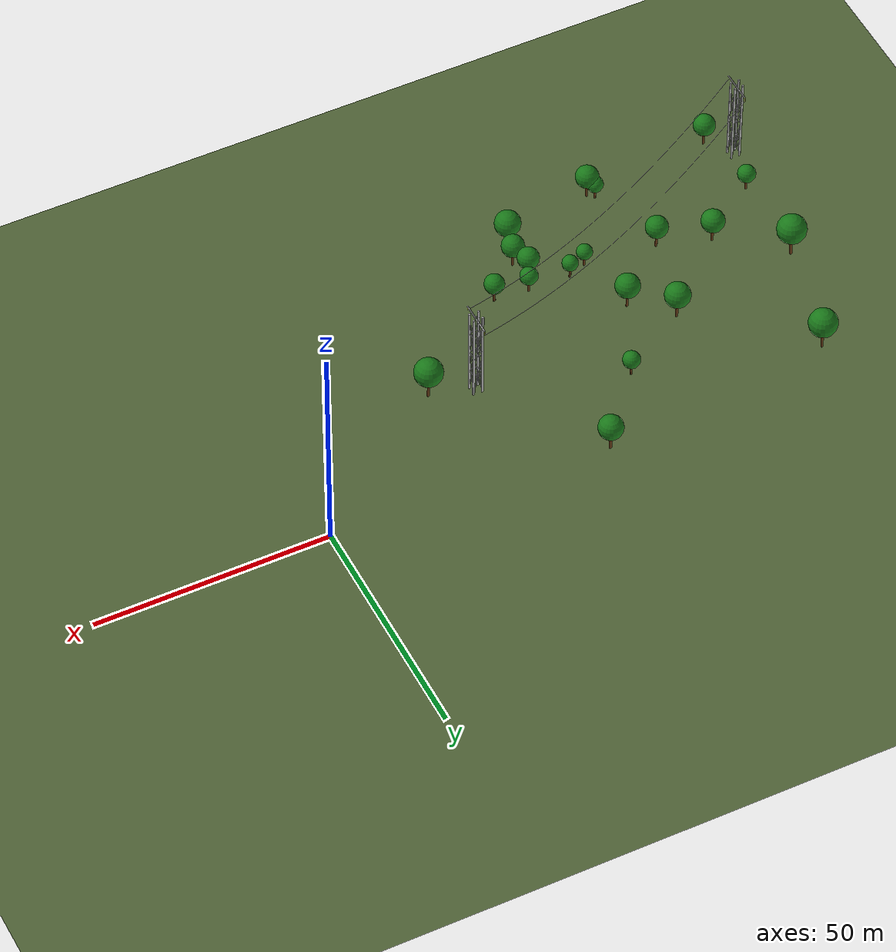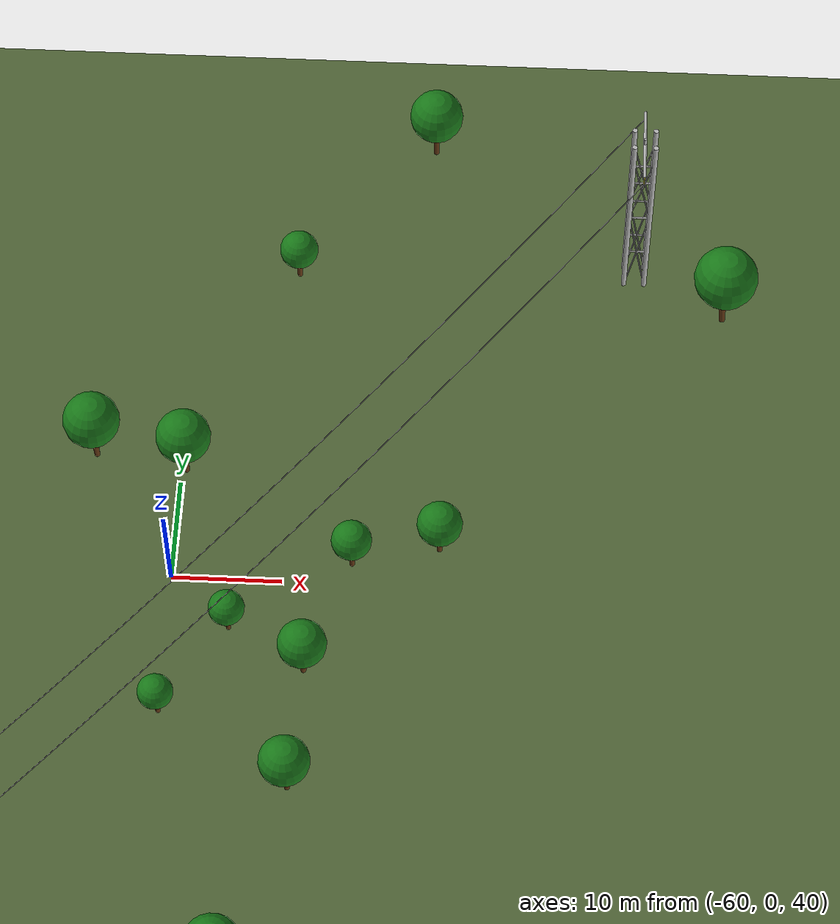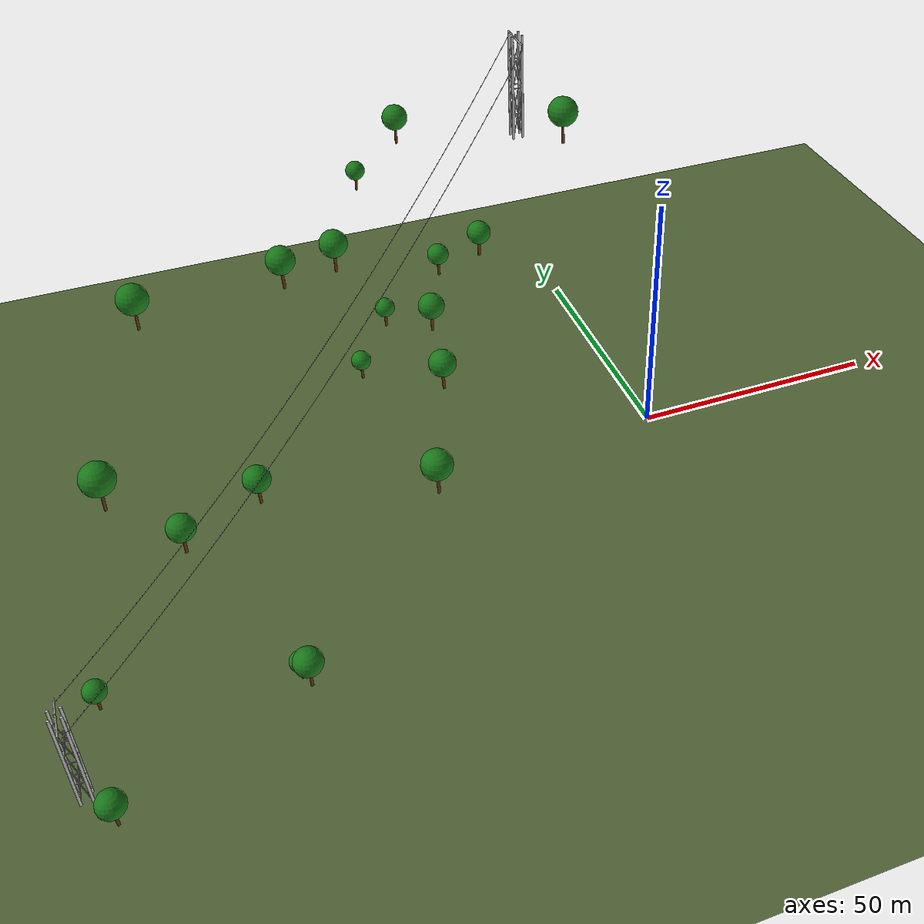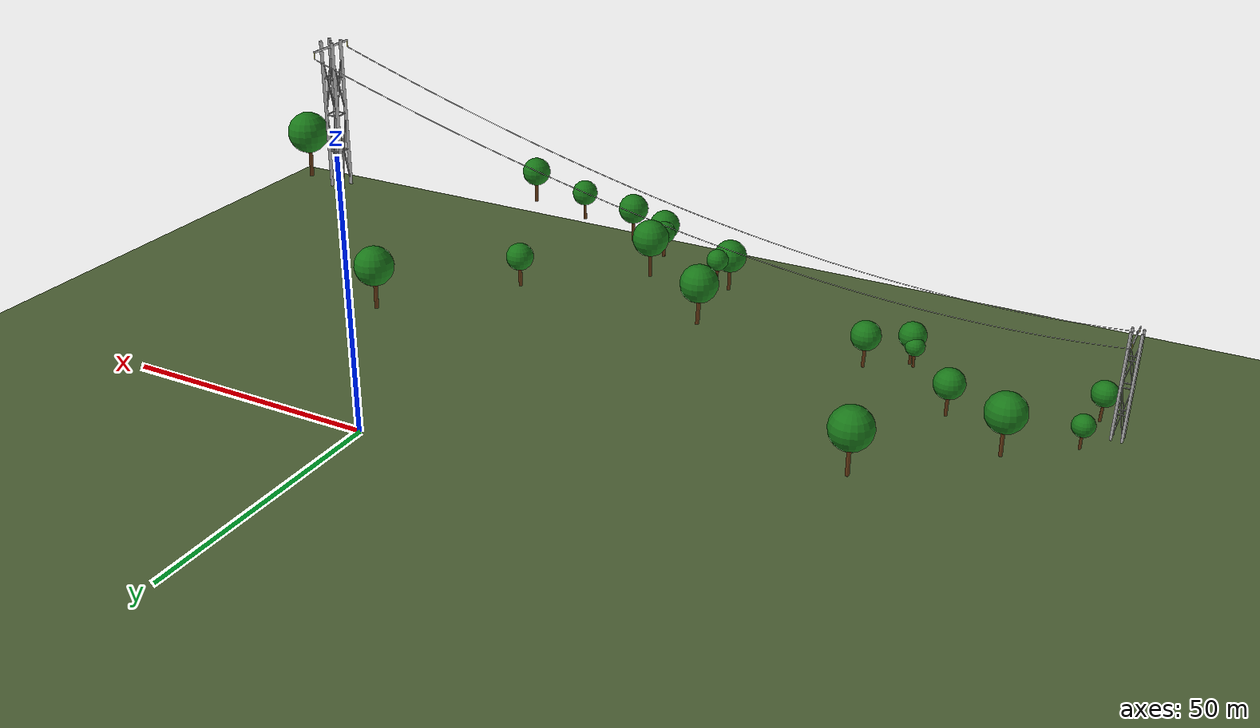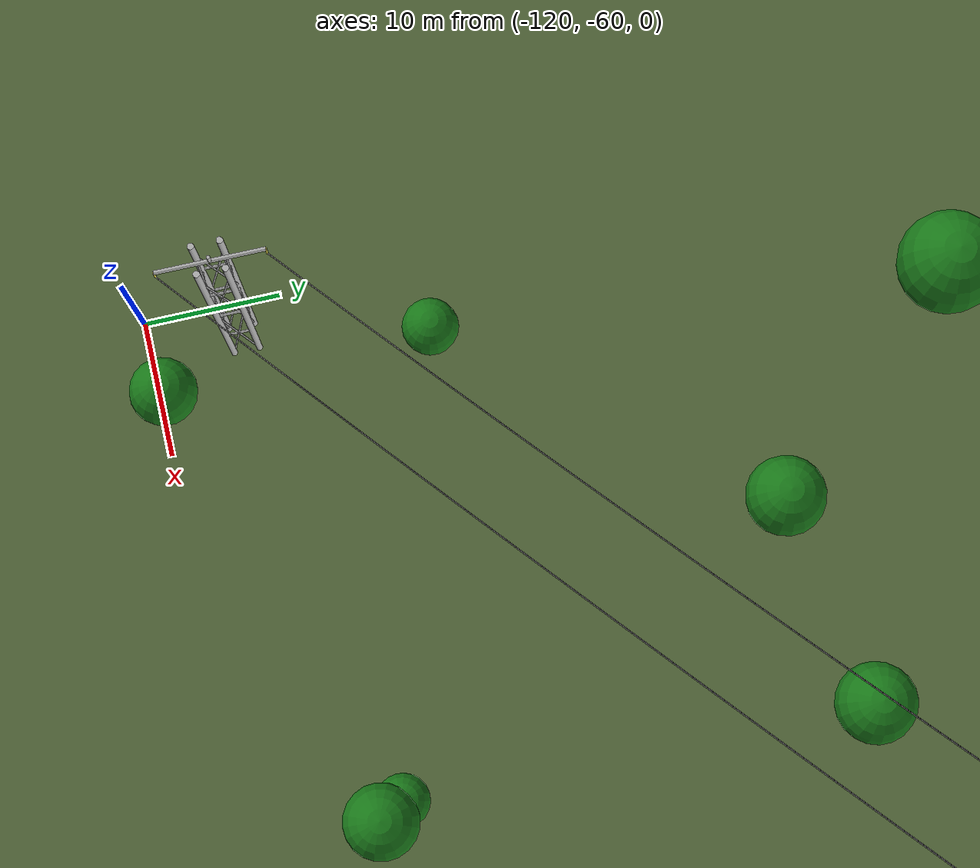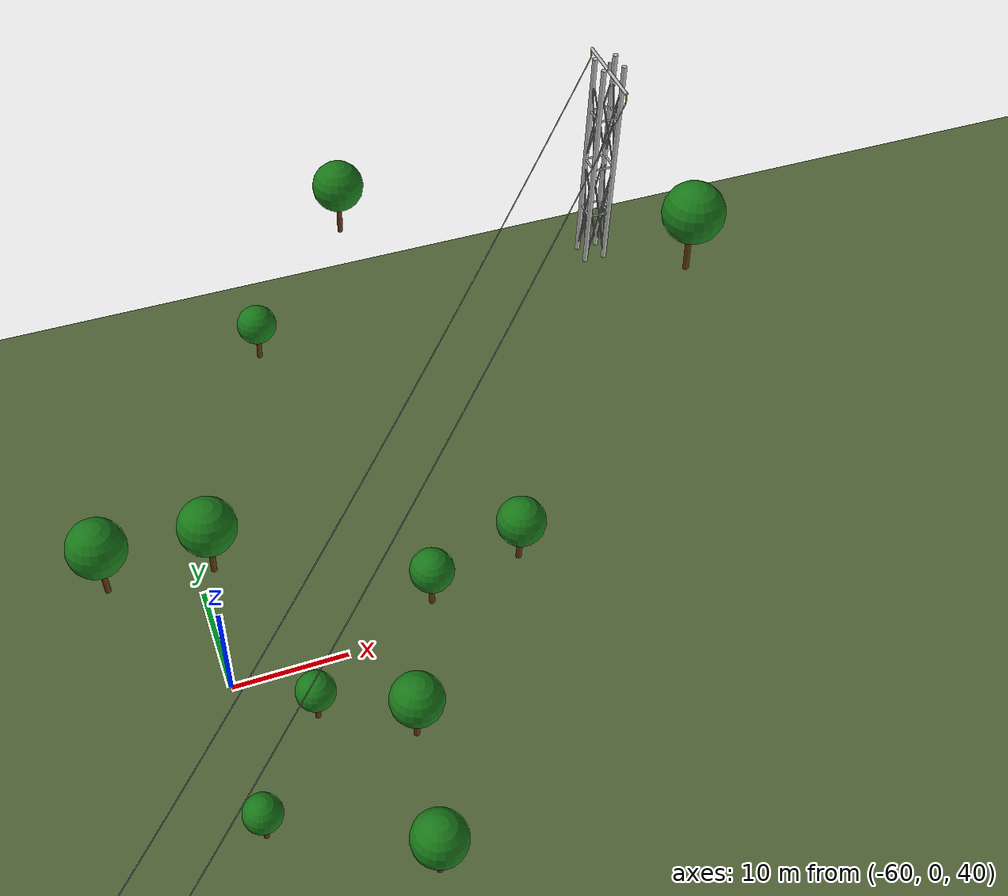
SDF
<sdf version="1.9">
 <world name="power_line_inspection">
  <plugin filename="gz-sim-physics-system" name="gz::sim::systems::Physics">
   <engine>gz-physics-dartsim-plugin</engine>
  </plugin>
  <plugin filename="gz-sim-user-commands-system" name="gz::sim::systems::UserCommands"/>
  <plugin filename="gz-sim-scene-broadcaster-system" name="gz::sim::systems::SceneBroadcaster"/>
  <plugin filename="gz-sim-sensors-system" name="gz::sim::systems::Sensors">
   <render_engine>ogre2</render_engine>
  </plugin>
  <plugin filename="gz-sim-imu-system" name="gz::sim::systems::Imu"/>
  <plugin filename="gz-sim-air-pressure-system" name="gz::sim::systems::AirPressure"/>
  <plugin filename="gz-sim-magnetometer-system" name="gz::sim::systems::Magnetometer"/>
  <plugin filename="gz-sim-navsat-system" name="gz::sim::systems::NavSat"/>
  <plugin filename="gz-sim-contact-system" name="gz::sim::systems::Contact"/>
  <physics name="1ms" type="ignored">
   <max_step_size>0.001</max_step_size>
   <real_time_factor>1.0</real_time_factor>
   <real_time_update_rate>1000</real_time_update_rate>
  </physics>
  <gravity>0 0 -9.8066</gravity>
  <magnetic_field>3.20e-05 -5.00e-07 3.50e-05</magnetic_field>
  <atmosphere type="adiabatic"/>
  <spherical_coordinates>
   <surface_model>EARTH_WGS84</surface_model>
   <latitude_deg>30.5728</latitude_deg>
   <longitude_deg>104.0668</longitude_deg>
   <elevation>500.0</elevation>
   <heading_deg>0</heading_deg>
  </spherical_coordinates>
  <scene>
   <ambient>0.55 0.55 0.55 1</ambient>
   <background>0.53 0.81 0.98 1</background>
   <shadows>true</shadows>
  </scene>
  <light type="directional" name="sun">
   <pose>0 0 500 0 0.4 0.6</pose>
   <diffuse>0.95 0.90 0.80 1</diffuse>
   <specular>0.30 0.30 0.30 1</specular>
   <direction>-0.5 0.3 -0.8</direction>
   <attenuation>
    <range>2000</range>
    <constant>0.9</constant>
    <linear>0.01</linear>
    <quadratic>0.0005</quadratic>
   </attenuation>
  </light>
  <light type="directional" name="fill_light">
   <cast_shadows>false</cast_shadows>
   <pose>0 0 100 0 -0.3 2.5</pose>
   <diffuse>0.4 0.45 0.55 1</diffuse>
   <specular>0.05 0.05 0.05 1</specular>
   <direction>0.5 -0.3 -0.5</direction>
  </light>
  <model name="ground_plane">
   <static>true</static>
   <pose>0 0 -0.01 0 0 0</pose>
   <link name="link">
    <collision name="collision">
     <geometry><plane><normal>0 0 1</normal><size>600 600</size></plane></geometry>
     <surface><friction><ode><mu>1.0</mu><mu2>1.0</mu2></ode></friction></surface>
    </collision>
    <visual name="visual">
     <cast_shadows>false</cast_shadows>
     <geometry><plane><normal>0 0 1</normal><size>600 600</size></plane></geometry>
     <material>
      <ambient>0.28 0.35 0.18 1</ambient>
      <diffuse>0.32 0.40 0.22 1</diffuse>
      <specular>0.02 0.02 0.02 1</specular>
     </material>
    </visual>
   </link>
  </model>
  <model name="base_tower_col-1-1">
   <static>true</static>
   <pose>-117.216 -53.795 14.000 0.00000 0.00000 0.00000</pose>
   <link name="link">
    <visual name="v">
     <geometry><cylinder><radius>0.22</radius><length>20.0000</length></cylinder></geometry>
     <material><ambient>0.72 0.72 0.72 1</ambient><diffuse>0.72 0.72 0.72 1</diffuse></material>
    </visual>
    <collision name="c">
     <geometry><cylinder><radius>0.22</radius><length>20.0000</length></cylinder></geometry>
    </collision>
   </link>
  </model>
  <model name="base_tower_col-11">
   <static>true</static>
   <pose>-117.216 -51.995 14.000 0.00000 0.00000 0.00000</pose>
   <link name="link">
    <visual name="v">
     <geometry><cylinder><radius>0.22</radius><length>20.0000</length></cylinder></geometry>
     <material><ambient>0.72 0.72 0.72 1</ambient><diffuse>0.72 0.72 0.72 1</diffuse></material>
    </visual>
    <collision name="c">
     <geometry><cylinder><radius>0.22</radius><length>20.0000</length></cylinder></geometry>
    </collision>
   </link>
  </model>
  <model name="base_tower_col1-1">
   <static>true</static>
   <pose>-115.416 -53.795 14.000 0.00000 0.00000 0.00000</pose>
   <link name="link">
    <visual name="v">
     <geometry><cylinder><radius>0.22</radius><length>20.0000</length></cylinder></geometry>
     <material><ambient>0.72 0.72 0.72 1</ambient><diffuse>0.72 0.72 0.72 1</diffuse></material>
    </visual>
    <collision name="c">
     <geometry><cylinder><radius>0.22</radius><length>20.0000</length></cylinder></geometry>
    </collision>
   </link>
  </model>
  <model name="base_tower_col11">
   <static>true</static>
   <pose>-115.416 -51.995 14.000 0.00000 0.00000 0.00000</pose>
   <link name="link">
    <visual name="v">
     <geometry><cylinder><radius>0.22</radius><length>20.0000</length></cylinder></geometry>
     <material><ambient>0.72 0.72 0.72 1</ambient><diffuse>0.72 0.72 0.72 1</diffuse></material>
    </visual>
    <collision name="c">
     <geometry><cylinder><radius>0.22</radius><length>20.0000</length></cylinder></geometry>
    </collision>
   </link>
  </model>
  <model name="base_tower_b1_e0">
   <static>true</static>
   <pose>-117.216 -52.895 9.000 -1.57080 0.00000 0.00000</pose>
   <link name="link">
    <visual name="v">
     <geometry><cylinder><radius>0.09</radius><length>1.8000</length></cylinder></geometry>
     <material><ambient>0.68 0.68 0.68 1</ambient><diffuse>0.68 0.68 0.68 1</diffuse></material>
    </visual>
    <collision name="c">
     <geometry><cylinder><radius>0.09</radius><length>1.8000</length></cylinder></geometry>
    </collision>
   </link>
  </model>
  <model name="base_tower_b1_e1">
   <static>true</static>
   <pose>-116.316 -51.995 9.000 0.00000 1.57080 0.00000</pose>
   <link name="link">
    <visual name="v">
     <geometry><cylinder><radius>0.09</radius><length>1.8000</length></cylinder></geometry>
     <material><ambient>0.68 0.68 0.68 1</ambient><diffuse>0.68 0.68 0.68 1</diffuse></material>
    </visual>
    <collision name="c">
     <geometry><cylinder><radius>0.09</radius><length>1.8000</length></cylinder></geometry>
    </collision>
   </link>
  </model>
  <model name="base_tower_b1_e2">
   <static>true</static>
   <pose>-115.416 -52.895 9.000 1.57080 0.00000 0.00000</pose>
   <link name="link">
    <visual name="v">
     <geometry><cylinder><radius>0.09</radius><length>1.8000</length></cylinder></geometry>
     <material><ambient>0.68 0.68 0.68 1</ambient><diffuse>0.68 0.68 0.68 1</diffuse></material>
    </visual>
    <collision name="c">
     <geometry><cylinder><radius>0.09</radius><length>1.8000</length></cylinder></geometry>
    </collision>
   </link>
  </model>
  <model name="base_tower_b1_e3">
   <static>true</static>
   <pose>-116.316 -53.795 9.000 0.00000 -1.57080 0.00000</pose>
   <link name="link">
    <visual name="v">
     <geometry><cylinder><radius>0.09</radius><length>1.8000</length></cylinder></geometry>
     <material><ambient>0.68 0.68 0.68 1</ambient><diffuse>0.68 0.68 0.68 1</diffuse></material>
    </visual>
    <collision name="c">
     <geometry><cylinder><radius>0.09</radius><length>1.8000</length></cylinder></geometry>
    </collision>
   </link>
  </model>
  <model name="base_tower_b2_e0">
   <static>true</static>
   <pose>-117.216 -52.895 14.000 -1.57080 0.00000 0.00000</pose>
   <link name="link">
    <visual name="v">
     <geometry><cylinder><radius>0.09</radius><length>1.8000</length></cylinder></geometry>
     <material><ambient>0.68 0.68 0.68 1</ambient><diffuse>0.68 0.68 0.68 1</diffuse></material>
    </visual>
    <collision name="c">
     <geometry><cylinder><radius>0.09</radius><length>1.8000</length></cylinder></geometry>
    </collision>
   </link>
  </model>
  <model name="base_tower_b2_e1">
   <static>true</static>
   <pose>-116.316 -51.995 14.000 0.00000 1.57080 0.00000</pose>
   <link name="link">
    <visual name="v">
     <geometry><cylinder><radius>0.09</radius><length>1.8000</length></cylinder></geometry>
     <material><ambient>0.68 0.68 0.68 1</ambient><diffuse>0.68 0.68 0.68 1</diffuse></material>
    </visual>
    <collision name="c">
     <geometry><cylinder><radius>0.09</radius><length>1.8000</length></cylinder></geometry>
    </collision>
   </link>
  </model>
  <model name="base_tower_b2_e2">
   <static>true</static>
   <pose>-115.416 -52.895 14.000 1.57080 0.00000 0.00000</pose>
   <link name="link">
    <visual name="v">
     <geometry><cylinder><radius>0.09</radius><length>1.8000</length></cylinder></geometry>
     <material><ambient>0.68 0.68 0.68 1</ambient><diffuse>0.68 0.68 0.68 1</diffuse></material>
    </visual>
    <collision name="c">
     <geometry><cylinder><radius>0.09</radius><length>1.8000</length></cylinder></geometry>
    </collision>
   </link>
  </model>
  <model name="base_tower_b2_e3">
   <static>true</static>
   <pose>-116.316 -53.795 14.000 0.00000 -1.57080 0.00000</pose>
   <link name="link">
    <visual name="v">
     <geometry><cylinder><radius>0.09</radius><length>1.8000</length></cylinder></geometry>
     <material><ambient>0.68 0.68 0.68 1</ambient><diffuse>0.68 0.68 0.68 1</diffuse></material>
    </visual>
    <collision name="c">
     <geometry><cylinder><radius>0.09</radius><length>1.8000</length></cylinder></geometry>
    </collision>
   </link>
  </model>
  <model name="base_tower_b3_e0">
   <static>true</static>
   <pose>-117.216 -52.895 19.000 -1.57080 0.00000 0.00000</pose>
   <link name="link">
    <visual name="v">
     <geometry><cylinder><radius>0.09</radius><length>1.8000</length></cylinder></geometry>
     <material><ambient>0.68 0.68 0.68 1</ambient><diffuse>0.68 0.68 0.68 1</diffuse></material>
    </visual>
    <collision name="c">
     <geometry><cylinder><radius>0.09</radius><length>1.8000</length></cylinder></geometry>
    </collision>
   </link>
  </model>
  <model name="base_tower_b3_e1">
   <static>true</static>
   <pose>-116.316 -51.995 19.000 0.00000 1.57080 0.00000</pose>
   <link name="link">
    <visual name="v">
     <geometry><cylinder><radius>0.09</radius><length>1.8000</length></cylinder></geometry>
     <material><ambient>0.68 0.68 0.68 1</ambient><diffuse>0.68 0.68 0.68 1</diffuse></material>
    </visual>
    <collision name="c">
     <geometry><cylinder><radius>0.09</radius><length>1.8000</length></cylinder></geometry>
    </collision>
   </link>
  </model>
  <model name="base_tower_b3_e2">
   <static>true</static>
   <pose>-115.416 -52.895 19.000 1.57080 0.00000 0.00000</pose>
   <link name="link">
    <visual name="v">
     <geometry><cylinder><radius>0.09</radius><length>1.8000</length></cylinder></geometry>
     <material><ambient>0.68 0.68 0.68 1</ambient><diffuse>0.68 0.68 0.68 1</diffuse></material>
    </visual>
    <collision name="c">
     <geometry><cylinder><radius>0.09</radius><length>1.8000</length></cylinder></geometry>
    </collision>
   </link>
  </model>
  <model name="base_tower_b3_e3">
   <static>true</static>
   <pose>-116.316 -53.795 19.000 0.00000 -1.57080 0.00000</pose>
   <link name="link">
    <visual name="v">
     <geometry><cylinder><radius>0.09</radius><length>1.8000</length></cylinder></geometry>
     <material><ambient>0.68 0.68 0.68 1</ambient><diffuse>0.68 0.68 0.68 1</diffuse></material>
    </visual>
    <collision name="c">
     <geometry><cylinder><radius>0.09</radius><length>1.8000</length></cylinder></geometry>
    </collision>
   </link>
  </model>
  <model name="base_tower_diag0_0a">
   <static>true</static>
   <pose>-117.216 -52.895 9.000 -0.17809 0.00000 0.00000</pose>
   <link name="link">
    <visual name="v">
     <geometry><cylinder><radius>0.063</radius><length>10.1607</length></cylinder></geometry>
     <material><ambient>0.65 0.65 0.65 1</ambient><diffuse>0.65 0.65 0.65 1</diffuse></material>
    </visual>
    <collision name="c">
     <geometry><cylinder><radius>0.063</radius><length>10.1607</length></cylinder></geometry>
    </collision>
   </link>
  </model>
  <model name="base_tower_diag0_0b">
   <static>true</static>
   <pose>-117.216 -52.895 9.000 0.17809 0.00000 0.00000</pose>
   <link name="link">
    <visual name="v">
     <geometry><cylinder><radius>0.063</radius><length>10.1607</length></cylinder></geometry>
     <material><ambient>0.65 0.65 0.65 1</ambient><diffuse>0.65 0.65 0.65 1</diffuse></material>
    </visual>
    <collision name="c">
     <geometry><cylinder><radius>0.063</radius><length>10.1607</length></cylinder></geometry>
    </collision>
   </link>
  </model>
  <model name="base_tower_diag0_1a">
   <static>true</static>
   <pose>-117.216 -52.895 18.000 -0.22131 0.00000 0.00000</pose>
   <link name="link">
    <visual name="v">
     <geometry><cylinder><radius>0.063</radius><length>8.2000</length></cylinder></geometry>
     <material><ambient>0.65 0.65 0.65 1</ambient><diffuse>0.65 0.65 0.65 1</diffuse></material>
    </visual>
    <collision name="c">
     <geometry><cylinder><radius>0.063</radius><length>8.2000</length></cylinder></geometry>
    </collision>
   </link>
  </model>
  <model name="base_tower_diag0_1b">
   <static>true</static>
   <pose>-117.216 -52.895 18.000 0.22131 0.00000 0.00000</pose>
   <link name="link">
    <visual name="v">
     <geometry><cylinder><radius>0.063</radius><length>8.2000</length></cylinder></geometry>
     <material><ambient>0.65 0.65 0.65 1</ambient><diffuse>0.65 0.65 0.65 1</diffuse></material>
    </visual>
    <collision name="c">
     <geometry><cylinder><radius>0.063</radius><length>8.2000</length></cylinder></geometry>
    </collision>
   </link>
  </model>
  <model name="base_tower_diag1_0a">
   <static>true</static>
   <pose>-115.416 -52.895 9.000 -0.17809 0.00000 0.00000</pose>
   <link name="link">
    <visual name="v">
     <geometry><cylinder><radius>0.063</radius><length>10.1607</length></cylinder></geometry>
     <material><ambient>0.65 0.65 0.65 1</ambient><diffuse>0.65 0.65 0.65 1</diffuse></material>
    </visual>
    <collision name="c">
     <geometry><cylinder><radius>0.063</radius><length>10.1607</length></cylinder></geometry>
    </collision>
   </link>
  </model>
  <model name="base_tower_diag1_0b">
   <static>true</static>
   <pose>-115.416 -52.895 9.000 0.17809 0.00000 0.00000</pose>
   <link name="link">
    <visual name="v">
     <geometry><cylinder><radius>0.063</radius><length>10.1607</length></cylinder></geometry>
     <material><ambient>0.65 0.65 0.65 1</ambient><diffuse>0.65 0.65 0.65 1</diffuse></material>
    </visual>
    <collision name="c">
     <geometry><cylinder><radius>0.063</radius><length>10.1607</length></cylinder></geometry>
    </collision>
   </link>
  </model>
  <model name="base_tower_diag1_1a">
   <static>true</static>
   <pose>-115.416 -52.895 18.000 -0.22131 0.00000 0.00000</pose>
   <link name="link">
    <visual name="v">
     <geometry><cylinder><radius>0.063</radius><length>8.2000</length></cylinder></geometry>
     <material><ambient>0.65 0.65 0.65 1</ambient><diffuse>0.65 0.65 0.65 1</diffuse></material>
    </visual>
    <collision name="c">
     <geometry><cylinder><radius>0.063</radius><length>8.2000</length></cylinder></geometry>
    </collision>
   </link>
  </model>
  <model name="base_tower_diag1_1b">
   <static>true</static>
   <pose>-115.416 -52.895 18.000 0.22131 0.00000 0.00000</pose>
   <link name="link">
    <visual name="v">
     <geometry><cylinder><radius>0.063</radius><length>8.2000</length></cylinder></geometry>
     <material><ambient>0.65 0.65 0.65 1</ambient><diffuse>0.65 0.65 0.65 1</diffuse></material>
    </visual>
    <collision name="c">
     <geometry><cylinder><radius>0.063</radius><length>8.2000</length></cylinder></geometry>
    </collision>
   </link>
  </model>
  <model name="base_tower_diag2_0a">
   <static>true</static>
   <pose>-116.316 -53.795 9.000 0.00000 0.17809 0.00000</pose>
   <link name="link">
    <visual name="v">
     <geometry><cylinder><radius>0.063</radius><length>10.1607</length></cylinder></geometry>
     <material><ambient>0.65 0.65 0.65 1</ambient><diffuse>0.65 0.65 0.65 1</diffuse></material>
    </visual>
    <collision name="c">
     <geometry><cylinder><radius>0.063</radius><length>10.1607</length></cylinder></geometry>
    </collision>
   </link>
  </model>
  <model name="base_tower_diag2_0b">
   <static>true</static>
   <pose>-116.316 -53.795 9.000 0.00000 -0.17809 0.00000</pose>
   <link name="link">
    <visual name="v">
     <geometry><cylinder><radius>0.063</radius><length>10.1607</length></cylinder></geometry>
     <material><ambient>0.65 0.65 0.65 1</ambient><diffuse>0.65 0.65 0.65 1</diffuse></material>
    </visual>
    <collision name="c">
     <geometry><cylinder><radius>0.063</radius><length>10.1607</length></cylinder></geometry>
    </collision>
   </link>
  </model>
  <model name="base_tower_diag2_1a">
   <static>true</static>
   <pose>-116.316 -53.795 18.000 0.00000 0.22131 0.00000</pose>
   <link name="link">
    <visual name="v">
     <geometry><cylinder><radius>0.063</radius><length>8.2000</length></cylinder></geometry>
     <material><ambient>0.65 0.65 0.65 1</ambient><diffuse>0.65 0.65 0.65 1</diffuse></material>
    </visual>
    <collision name="c">
     <geometry><cylinder><radius>0.063</radius><length>8.2000</length></cylinder></geometry>
    </collision>
   </link>
  </model>
  <model name="base_tower_diag2_1b">
   <static>true</static>
   <pose>-116.316 -53.795 18.000 0.00000 -0.22131 0.00000</pose>
   <link name="link">
    <visual name="v">
     <geometry><cylinder><radius>0.063</radius><length>8.2000</length></cylinder></geometry>
     <material><ambient>0.65 0.65 0.65 1</ambient><diffuse>0.65 0.65 0.65 1</diffuse></material>
    </visual>
    <collision name="c">
     <geometry><cylinder><radius>0.063</radius><length>8.2000</length></cylinder></geometry>
    </collision>
   </link>
  </model>
  <model name="base_tower_diag3_0a">
   <static>true</static>
   <pose>-116.316 -51.995 9.000 0.00000 0.17809 0.00000</pose>
   <link name="link">
    <visual name="v">
     <geometry><cylinder><radius>0.063</radius><length>10.1607</length></cylinder></geometry>
     <material><ambient>0.65 0.65 0.65 1</ambient><diffuse>0.65 0.65 0.65 1</diffuse></material>
    </visual>
    <collision name="c">
     <geometry><cylinder><radius>0.063</radius><length>10.1607</length></cylinder></geometry>
    </collision>
   </link>
  </model>
  <model name="base_tower_diag3_0b">
   <static>true</static>
   <pose>-116.316 -51.995 9.000 0.00000 -0.17809 0.00000</pose>
   <link name="link">
    <visual name="v">
     <geometry><cylinder><radius>0.063</radius><length>10.1607</length></cylinder></geometry>
     <material><ambient>0.65 0.65 0.65 1</ambient><diffuse>0.65 0.65 0.65 1</diffuse></material>
    </visual>
    <collision name="c">
     <geometry><cylinder><radius>0.063</radius><length>10.1607</length></cylinder></geometry>
    </collision>
   </link>
  </model>
  <model name="base_tower_diag3_1a">
   <static>true</static>
   <pose>-116.316 -51.995 18.000 0.00000 0.22131 0.00000</pose>
   <link name="link">
    <visual name="v">
     <geometry><cylinder><radius>0.063</radius><length>8.2000</length></cylinder></geometry>
     <material><ambient>0.65 0.65 0.65 1</ambient><diffuse>0.65 0.65 0.65 1</diffuse></material>
    </visual>
    <collision name="c">
     <geometry><cylinder><radius>0.063</radius><length>8.2000</length></cylinder></geometry>
    </collision>
   </link>
  </model>
  <model name="base_tower_diag3_1b">
   <static>true</static>
   <pose>-116.316 -51.995 18.000 0.00000 -0.22131 0.00000</pose>
   <link name="link">
    <visual name="v">
     <geometry><cylinder><radius>0.063</radius><length>8.2000</length></cylinder></geometry>
     <material><ambient>0.65 0.65 0.65 1</ambient><diffuse>0.65 0.65 0.65 1</diffuse></material>
    </visual>
    <collision name="c">
     <geometry><cylinder><radius>0.063</radius><length>8.2000</length></cylinder></geometry>
    </collision>
   </link>
  </model>
  <model name="base_tower_arm">
   <static>true</static>
   <pose>-116.316 -52.895 23.200 -1.57080 0.00000 0.00000</pose>
   <link name="link">
    <visual name="v">
     <geometry><cylinder><radius>0.14</radius><length>7.0000</length></cylinder></geometry>
     <material><ambient>0.72 0.72 0.72 1</ambient><diffuse>0.72 0.72 0.72 1</diffuse></material>
    </visual>
    <collision name="c">
     <geometry><cylinder><radius>0.14</radius><length>7.0000</length></cylinder></geometry>
    </collision>
   </link>
  </model>
  <model name="base_tower_vsup">
   <static>true</static>
   <pose>-116.316 -52.895 23.600 3.14159 0.00000 0.00000</pose>
   <link name="link">
    <visual name="v">
     <geometry><cylinder><radius>0.12</radius><length>0.8000</length></cylinder></geometry>
     <material><ambient>0.72 0.72 0.72 1</ambient><diffuse>0.72 0.72 0.72 1</diffuse></material>
    </visual>
    <collision name="c">
     <geometry><cylinder><radius>0.12</radius><length>0.8000</length></cylinder></geometry>
    </collision>
   </link>
  </model>
  <model name="base_tower_insL">
   <static>true</static>
   <pose>-116.316 -56.395 22.750 3.14159 0.00000 0.00000</pose>
   <link name="link">
    <visual name="v">
     <geometry><cylinder><radius>0.06</radius><length>0.9000</length></cylinder></geometry>
     <material><ambient>0.9 0.85 0.3 1</ambient><diffuse>0.9 0.85 0.3 1</diffuse></material>
    </visual>
    <collision name="c">
     <geometry><cylinder><radius>0.06</radius><length>0.9000</length></cylinder></geometry>
    </collision>
   </link>
  </model>
  <model name="base_tower_insR">
   <static>true</static>
   <pose>-116.316 -49.395 22.750 3.14159 0.00000 0.00000</pose>
   <link name="link">
    <visual name="v">
     <geometry><cylinder><radius>0.06</radius><length>0.9000</length></cylinder></geometry>
     <material><ambient>0.9 0.85 0.3 1</ambient><diffuse>0.9 0.85 0.3 1</diffuse></material>
    </visual>
    <collision name="c">
     <geometry><cylinder><radius>0.06</radius><length>0.9000</length></cylinder></geometry>
    </collision>
   </link>
  </model>
  <model name="peak_tower_col-1-1">
   <static>true</static>
   <pose>-20.186 22.671 66.602 0.00000 0.00000 0.00000</pose>
   <link name="link">
    <visual name="v">
     <geometry><cylinder><radius>0.22</radius><length>20.0000</length></cylinder></geometry>
     <material><ambient>0.72 0.72 0.72 1</ambient><diffuse>0.72 0.72 0.72 1</diffuse></material>
    </visual>
    <collision name="c">
     <geometry><cylinder><radius>0.22</radius><length>20.0000</length></cylinder></geometry>
    </collision>
   </link>
  </model>
  <model name="peak_tower_col-11">
   <static>true</static>
   <pose>-20.186 24.471 66.602 0.00000 0.00000 0.00000</pose>
   <link name="link">
    <visual name="v">
     <geometry><cylinder><radius>0.22</radius><length>20.0000</length></cylinder></geometry>
     <material><ambient>0.72 0.72 0.72 1</ambient><diffuse>0.72 0.72 0.72 1</diffuse></material>
    </visual>
    <collision name="c">
     <geometry><cylinder><radius>0.22</radius><length>20.0000</length></cylinder></geometry>
    </collision>
   </link>
  </model>
  <model name="peak_tower_col1-1">
   <static>true</static>
   <pose>-18.386 22.671 66.602 0.00000 0.00000 0.00000</pose>
   <link name="link">
    <visual name="v">
     <geometry><cylinder><radius>0.22</radius><length>20.0000</length></cylinder></geometry>
     <material><ambient>0.72 0.72 0.72 1</ambient><diffuse>0.72 0.72 0.72 1</diffuse></material>
    </visual>
    <collision name="c">
     <geometry><cylinder><radius>0.22</radius><length>20.0000</length></cylinder></geometry>
    </collision>
   </link>
  </model>
  <model name="peak_tower_col11">
   <static>true</static>
   <pose>-18.386 24.471 66.602 0.00000 0.00000 0.00000</pose>
   <link name="link">
    <visual name="v">
     <geometry><cylinder><radius>0.22</radius><length>20.0000</length></cylinder></geometry>
     <material><ambient>0.72 0.72 0.72 1</ambient><diffuse>0.72 0.72 0.72 1</diffuse></material>
    </visual>
    <collision name="c">
     <geometry><cylinder><radius>0.22</radius><length>20.0000</length></cylinder></geometry>
    </collision>
   </link>
  </model>
  <model name="peak_tower_b1_e0">
   <static>true</static>
   <pose>-20.186 23.571 61.602 -1.57080 0.00000 0.00000</pose>
   <link name="link">
    <visual name="v">
     <geometry><cylinder><radius>0.09</radius><length>1.8000</length></cylinder></geometry>
     <material><ambient>0.68 0.68 0.68 1</ambient><diffuse>0.68 0.68 0.68 1</diffuse></material>
    </visual>
    <collision name="c">
     <geometry><cylinder><radius>0.09</radius><length>1.8000</length></cylinder></geometry>
    </collision>
   </link>
  </model>
  <model name="peak_tower_b1_e1">
   <static>true</static>
   <pose>-19.286 24.471 61.602 0.00000 1.57080 0.00000</pose>
   <link name="link">
    <visual name="v">
     <geometry><cylinder><radius>0.09</radius><length>1.8000</length></cylinder></geometry>
     <material><ambient>0.68 0.68 0.68 1</ambient><diffuse>0.68 0.68 0.68 1</diffuse></material>
    </visual>
    <collision name="c">
     <geometry><cylinder><radius>0.09</radius><length>1.8000</length></cylinder></geometry>
    </collision>
   </link>
  </model>
  <model name="peak_tower_b1_e2">
   <static>true</static>
   <pose>-18.386 23.571 61.602 1.57080 0.00000 0.00000</pose>
   <link name="link">
    <visual name="v">
     <geometry><cylinder><radius>0.09</radius><length>1.8000</length></cylinder></geometry>
     <material><ambient>0.68 0.68 0.68 1</ambient><diffuse>0.68 0.68 0.68 1</diffuse></material>
    </visual>
    <collision name="c">
     <geometry><cylinder><radius>0.09</radius><length>1.8000</length></cylinder></geometry>
    </collision>
   </link>
  </model>
  <model name="peak_tower_b1_e3">
   <static>true</static>
   <pose>-19.286 22.671 61.602 0.00000 -1.57080 0.00000</pose>
   <link name="link">
    <visual name="v">
     <geometry><cylinder><radius>0.09</radius><length>1.8000</length></cylinder></geometry>
     <material><ambient>0.68 0.68 0.68 1</ambient><diffuse>0.68 0.68 0.68 1</diffuse></material>
    </visual>
    <collision name="c">
     <geometry><cylinder><radius>0.09</radius><length>1.8000</length></cylinder></geometry>
    </collision>
   </link>
  </model>
  <model name="peak_tower_b2_e0">
   <static>true</static>
   <pose>-20.186 23.571 66.602 -1.57080 0.00000 0.00000</pose>
   <link name="link">
    <visual name="v">
     <geometry><cylinder><radius>0.09</radius><length>1.8000</length></cylinder></geometry>
     <material><ambient>0.68 0.68 0.68 1</ambient><diffuse>0.68 0.68 0.68 1</diffuse></material>
    </visual>
    <collision name="c">
     <geometry><cylinder><radius>0.09</radius><length>1.8000</length></cylinder></geometry>
    </collision>
   </link>
  </model>
  <model name="peak_tower_b2_e1">
   <static>true</static>
   <pose>-19.286 24.471 66.602 0.00000 1.57080 0.00000</pose>
   <link name="link">
    <visual name="v">
     <geometry><cylinder><radius>0.09</radius><length>1.8000</length></cylinder></geometry>
     <material><ambient>0.68 0.68 0.68 1</ambient><diffuse>0.68 0.68 0.68 1</diffuse></material>
    </visual>
    <collision name="c">
     <geometry><cylinder><radius>0.09</radius><length>1.8000</length></cylinder></geometry>
    </collision>
   </link>
  </model>
  <model name="peak_tower_b2_e2">
   <static>true</static>
   <pose>-18.386 23.571 66.602 1.57080 0.00000 0.00000</pose>
   <link name="link">
    <visual name="v">
     <geometry><cylinder><radius>0.09</radius><length>1.8000</length></cylinder></geometry>
     <material><ambient>0.68 0.68 0.68 1</ambient><diffuse>0.68 0.68 0.68 1</diffuse></material>
    </visual>
    <collision name="c">
     <geometry><cylinder><radius>0.09</radius><length>1.8000</length></cylinder></geometry>
    </collision>
   </link>
  </model>
  <model name="peak_tower_b2_e3">
   <static>true</static>
   <pose>-19.286 22.671 66.602 0.00000 -1.57080 0.00000</pose>
   <link name="link">
    <visual name="v">
     <geometry><cylinder><radius>0.09</radius><length>1.8000</length></cylinder></geometry>
     <material><ambient>0.68 0.68 0.68 1</ambient><diffuse>0.68 0.68 0.68 1</diffuse></material>
    </visual>
    <collision name="c">
     <geometry><cylinder><radius>0.09</radius><length>1.8000</length></cylinder></geometry>
    </collision>
   </link>
  </model>
  <model name="peak_tower_b3_e0">
   <static>true</static>
   <pose>-20.186 23.571 71.602 -1.57080 0.00000 0.00000</pose>
   <link name="link">
    <visual name="v">
     <geometry><cylinder><radius>0.09</radius><length>1.8000</length></cylinder></geometry>
     <material><ambient>0.68 0.68 0.68 1</ambient><diffuse>0.68 0.68 0.68 1</diffuse></material>
    </visual>
    <collision name="c">
     <geometry><cylinder><radius>0.09</radius><length>1.8000</length></cylinder></geometry>
    </collision>
   </link>
  </model>
  <model name="peak_tower_b3_e1">
   <static>true</static>
   <pose>-19.286 24.471 71.602 0.00000 1.57080 0.00000</pose>
   <link name="link">
    <visual name="v">
     <geometry><cylinder><radius>0.09</radius><length>1.8000</length></cylinder></geometry>
     <material><ambient>0.68 0.68 0.68 1</ambient><diffuse>0.68 0.68 0.68 1</diffuse></material>
    </visual>
    <collision name="c">
     <geometry><cylinder><radius>0.09</radius><length>1.8000</length></cylinder></geometry>
    </collision>
   </link>
  </model>
  <model name="peak_tower_b3_e2">
   <static>true</static>
   <pose>-18.386 23.571 71.602 1.57080 0.00000 0.00000</pose>
   <link name="link">
    <visual name="v">
     <geometry><cylinder><radius>0.09</radius><length>1.8000</length></cylinder></geometry>
     <material><ambient>0.68 0.68 0.68 1</ambient><diffuse>0.68 0.68 0.68 1</diffuse></material>
    </visual>
    <collision name="c">
     <geometry><cylinder><radius>0.09</radius><length>1.8000</length></cylinder></geometry>
    </collision>
   </link>
  </model>
  <model name="peak_tower_b3_e3">
   <static>true</static>
   <pose>-19.286 22.671 71.602 0.00000 -1.57080 0.00000</pose>
   <link name="link">
    <visual name="v">
     <geometry><cylinder><radius>0.09</radius><length>1.8000</length></cylinder></geometry>
     <material><ambient>0.68 0.68 0.68 1</ambient><diffuse>0.68 0.68 0.68 1</diffuse></material>
    </visual>
    <collision name="c">
     <geometry><cylinder><radius>0.09</radius><length>1.8000</length></cylinder></geometry>
    </collision>
   </link>
  </model>
  <model name="peak_tower_diag0_0a">
   <static>true</static>
   <pose>-20.186 23.571 61.602 -0.17809 0.00000 0.00000</pose>
   <link name="link">
    <visual name="v">
     <geometry><cylinder><radius>0.063</radius><length>10.1607</length></cylinder></geometry>
     <material><ambient>0.65 0.65 0.65 1</ambient><diffuse>0.65 0.65 0.65 1</diffuse></material>
    </visual>
    <collision name="c">
     <geometry><cylinder><radius>0.063</radius><length>10.1607</length></cylinder></geometry>
    </collision>
   </link>
  </model>
  <model name="peak_tower_diag0_0b">
   <static>true</static>
   <pose>-20.186 23.571 61.602 0.17809 0.00000 0.00000</pose>
   <link name="link">
    <visual name="v">
     <geometry><cylinder><radius>0.063</radius><length>10.1607</length></cylinder></geometry>
     <material><ambient>0.65 0.65 0.65 1</ambient><diffuse>0.65 0.65 0.65 1</diffuse></material>
    </visual>
    <collision name="c">
     <geometry><cylinder><radius>0.063</radius><length>10.1607</length></cylinder></geometry>
    </collision>
   </link>
  </model>
  <model name="peak_tower_diag0_1a">
   <static>true</static>
   <pose>-20.186 23.571 70.602 -0.22131 0.00000 0.00000</pose>
   <link name="link">
    <visual name="v">
     <geometry><cylinder><radius>0.063</radius><length>8.2000</length></cylinder></geometry>
     <material><ambient>0.65 0.65 0.65 1</ambient><diffuse>0.65 0.65 0.65 1</diffuse></material>
    </visual>
    <collision name="c">
     <geometry><cylinder><radius>0.063</radius><length>8.2000</length></cylinder></geometry>
    </collision>
   </link>
  </model>
  <model name="peak_tower_diag0_1b">
   <static>true</static>
   <pose>-20.186 23.571 70.602 0.22131 0.00000 0.00000</pose>
   <link name="link">
    <visual name="v">
     <geometry><cylinder><radius>0.063</radius><length>8.2000</length></cylinder></geometry>
     <material><ambient>0.65 0.65 0.65 1</ambient><diffuse>0.65 0.65 0.65 1</diffuse></material>
    </visual>
    <collision name="c">
     <geometry><cylinder><radius>0.063</radius><length>8.2000</length></cylinder></geometry>
    </collision>
   </link>
  </model>
  <model name="peak_tower_diag1_0a">
   <static>true</static>
   <pose>-18.386 23.571 61.602 -0.17809 0.00000 0.00000</pose>
   <link name="link">
    <visual name="v">
     <geometry><cylinder><radius>0.063</radius><length>10.1607</length></cylinder></geometry>
     <material><ambient>0.65 0.65 0.65 1</ambient><diffuse>0.65 0.65 0.65 1</diffuse></material>
    </visual>
    <collision name="c">
     <geometry><cylinder><radius>0.063</radius><length>10.1607</length></cylinder></geometry>
    </collision>
   </link>
  </model>
  <model name="peak_tower_diag1_0b">
   <static>true</static>
   <pose>-18.386 23.571 61.602 0.17809 0.00000 0.00000</pose>
   <link name="link">
    <visual name="v">
     <geometry><cylinder><radius>0.063</radius><length>10.1607</length></cylinder></geometry>
     <material><ambient>0.65 0.65 0.65 1</ambient><diffuse>0.65 0.65 0.65 1</diffuse></material>
    </visual>
    <collision name="c">
     <geometry><cylinder><radius>0.063</radius><length>10.1607</length></cylinder></geometry>
    </collision>
   </link>
  </model>
  <model name="peak_tower_diag1_1a">
   <static>true</static>
   <pose>-18.386 23.571 70.602 -0.22131 0.00000 0.00000</pose>
   <link name="link">
    <visual name="v">
     <geometry><cylinder><radius>0.063</radius><length>8.2000</length></cylinder></geometry>
     <material><ambient>0.65 0.65 0.65 1</ambient><diffuse>0.65 0.65 0.65 1</diffuse></material>
    </visual>
    <collision name="c">
     <geometry><cylinder><radius>0.063</radius><length>8.2000</length></cylinder></geometry>
    </collision>
   </link>
  </model>
  <model name="peak_tower_diag1_1b">
   <static>true</static>
   <pose>-18.386 23.571 70.602 0.22131 0.00000 0.00000</pose>
   <link name="link">
    <visual name="v">
     <geometry><cylinder><radius>0.063</radius><length>8.2000</length></cylinder></geometry>
     <material><ambient>0.65 0.65 0.65 1</ambient><diffuse>0.65 0.65 0.65 1</diffuse></material>
    </visual>
    <collision name="c">
     <geometry><cylinder><radius>0.063</radius><length>8.2000</length></cylinder></geometry>
    </collision>
   </link>
  </model>
  <model name="peak_tower_diag2_0a">
   <static>true</static>
   <pose>-19.286 22.671 61.602 0.00000 0.17809 0.00000</pose>
   <link name="link">
    <visual name="v">
     <geometry><cylinder><radius>0.063</radius><length>10.1607</length></cylinder></geometry>
     <material><ambient>0.65 0.65 0.65 1</ambient><diffuse>0.65 0.65 0.65 1</diffuse></material>
    </visual>
    <collision name="c">
     <geometry><cylinder><radius>0.063</radius><length>10.1607</length></cylinder></geometry>
    </collision>
   </link>
  </model>
  <model name="peak_tower_diag2_0b">
   <static>true</static>
   <pose>-19.286 22.671 61.602 0.00000 -0.17809 0.00000</pose>
   <link name="link">
    <visual name="v">
     <geometry><cylinder><radius>0.063</radius><length>10.1607</length></cylinder></geometry>
     <material><ambient>0.65 0.65 0.65 1</ambient><diffuse>0.65 0.65 0.65 1</diffuse></material>
    </visual>
    <collision name="c">
     <geometry><cylinder><radius>0.063</radius><length>10.1607</length></cylinder></geometry>
    </collision>
   </link>
  </model>
  <model name="peak_tower_diag2_1a">
   <static>true</static>
   <pose>-19.286 22.671 70.602 0.00000 0.22131 0.00000</pose>
   <link name="link">
    <visual name="v">
     <geometry><cylinder><radius>0.063</radius><length>8.2000</length></cylinder></geometry>
     <material><ambient>0.65 0.65 0.65 1</ambient><diffuse>0.65 0.65 0.65 1</diffuse></material>
    </visual>
    <collision name="c">
     <geometry><cylinder><radius>0.063</radius><length>8.2000</length></cylinder></geometry>
    </collision>
   </link>
  </model>
  <model name="peak_tower_diag2_1b">
   <static>true</static>
   <pose>-19.286 22.671 70.602 0.00000 -0.22131 0.00000</pose>
   <link name="link">
    <visual name="v">
     <geometry><cylinder><radius>0.063</radius><length>8.2000</length></cylinder></geometry>
     <material><ambient>0.65 0.65 0.65 1</ambient><diffuse>0.65 0.65 0.65 1</diffuse></material>
    </visual>
    <collision name="c">
     <geometry><cylinder><radius>0.063</radius><length>8.2000</length></cylinder></geometry>
    </collision>
   </link>
  </model>
  <model name="peak_tower_diag3_0a">
   <static>true</static>
   <pose>-19.286 24.471 61.602 0.00000 0.17809 0.00000</pose>
   <link name="link">
    <visual name="v">
     <geometry><cylinder><radius>0.063</radius><length>10.1607</length></cylinder></geometry>
     <material><ambient>0.65 0.65 0.65 1</ambient><diffuse>0.65 0.65 0.65 1</diffuse></material>
    </visual>
    <collision name="c">
     <geometry><cylinder><radius>0.063</radius><length>10.1607</length></cylinder></geometry>
    </collision>
   </link>
  </model>
  <model name="peak_tower_diag3_0b">
   <static>true</static>
   <pose>-19.286 24.471 61.602 0.00000 -0.17809 0.00000</pose>
   <link name="link">
    <visual name="v">
     <geometry><cylinder><radius>0.063</radius><length>10.1607</length></cylinder></geometry>
     <material><ambient>0.65 0.65 0.65 1</ambient><diffuse>0.65 0.65 0.65 1</diffuse></material>
    </visual>
    <collision name="c">
     <geometry><cylinder><radius>0.063</radius><length>10.1607</length></cylinder></geometry>
    </collision>
   </link>
  </model>
  <model name="peak_tower_diag3_1a">
   <static>true</static>
   <pose>-19.286 24.471 70.602 0.00000 0.22131 0.00000</pose>
   <link name="link">
    <visual name="v">
     <geometry><cylinder><radius>0.063</radius><length>8.2000</length></cylinder></geometry>
     <material><ambient>0.65 0.65 0.65 1</ambient><diffuse>0.65 0.65 0.65 1</diffuse></material>
    </visual>
    <collision name="c">
     <geometry><cylinder><radius>0.063</radius><length>8.2000</length></cylinder></geometry>
    </collision>
   </link>
  </model>
  <model name="peak_tower_diag3_1b">
   <static>true</static>
   <pose>-19.286 24.471 70.602 0.00000 -0.22131 0.00000</pose>
   <link name="link">
    <visual name="v">
     <geometry><cylinder><radius>0.063</radius><length>8.2000</length></cylinder></geometry>
     <material><ambient>0.65 0.65 0.65 1</ambient><diffuse>0.65 0.65 0.65 1</diffuse></material>
    </visual>
    <collision name="c">
     <geometry><cylinder><radius>0.063</radius><length>8.2000</length></cylinder></geometry>
    </collision>
   </link>
  </model>
  <model name="peak_tower_arm">
   <static>true</static>
   <pose>-19.286 23.571 75.802 -1.57080 0.00000 0.00000</pose>
   <link name="link">
    <visual name="v">
     <geometry><cylinder><radius>0.14</radius><length>7.0000</length></cylinder></geometry>
     <material><ambient>0.72 0.72 0.72 1</ambient><diffuse>0.72 0.72 0.72 1</diffuse></material>
    </visual>
    <collision name="c">
     <geometry><cylinder><radius>0.14</radius><length>7.0000</length></cylinder></geometry>
    </collision>
   </link>
  </model>
  <model name="peak_tower_vsup">
   <static>true</static>
   <pose>-19.286 23.571 76.202 3.14159 0.00000 0.00000</pose>
   <link name="link">
    <visual name="v">
     <geometry><cylinder><radius>0.12</radius><length>0.8000</length></cylinder></geometry>
     <material><ambient>0.72 0.72 0.72 1</ambient><diffuse>0.72 0.72 0.72 1</diffuse></material>
    </visual>
    <collision name="c">
     <geometry><cylinder><radius>0.12</radius><length>0.8000</length></cylinder></geometry>
    </collision>
   </link>
  </model>
  <model name="peak_tower_insL">
   <static>true</static>
   <pose>-19.286 20.071 75.352 3.14159 0.00000 0.00000</pose>
   <link name="link">
    <visual name="v">
     <geometry><cylinder><radius>0.06</radius><length>0.9000</length></cylinder></geometry>
     <material><ambient>0.9 0.85 0.3 1</ambient><diffuse>0.9 0.85 0.3 1</diffuse></material>
    </visual>
    <collision name="c">
     <geometry><cylinder><radius>0.06</radius><length>0.9000</length></cylinder></geometry>
    </collision>
   </link>
  </model>
  <model name="peak_tower_insR">
   <static>true</static>
   <pose>-19.286 27.071 75.352 3.14159 0.00000 0.00000</pose>
   <link name="link">
    <visual name="v">
     <geometry><cylinder><radius>0.06</radius><length>0.9000</length></cylinder></geometry>
     <material><ambient>0.9 0.85 0.3 1</ambient><diffuse>0.9 0.85 0.3 1</diffuse></material>
    </visual>
    <collision name="c">
     <geometry><cylinder><radius>0.06</radius><length>0.9000</length></cylinder></geometry>
    </collision>
   </link>
  </model>
  <model name="wire_L_s00">
   <static>true</static>
   <pose>-114.930 -55.302 22.678 -1.23701 0.87561 -0.64313</pose>
   <link name="link">
    <visual name="v">
     <geometry><cylinder><radius>0.04</radius><length>3.6101</length></cylinder></geometry>
     <material><ambient>0.08 0.08 0.08 1</ambient><diffuse>0.08 0.08 0.08 1</diffuse></material>
    </visual>
    <collision name="c">
     <geometry><cylinder><radius>0.04</radius><length>3.6101</length></cylinder></geometry>
    </collision>
   </link>
  </model>
  <model name="wire_L_s01">
   <static>true</static>
   <pose>-112.157 -53.118 23.458 -1.21921 0.87248 -0.62947</pose>
   <link name="link">
    <visual name="v">
     <geometry><cylinder><radius>0.04</radius><length>3.6195</length></cylinder></geometry>
     <material><ambient>0.08 0.08 0.08 1</ambient><diffuse>0.08 0.08 0.08 1</diffuse></material>
    </visual>
    <collision name="c">
     <geometry><cylinder><radius>0.04</radius><length>3.6195</length></cylinder></geometry>
    </collision>
   </link>
  </model>
  <model name="wire_L_s02">
   <static>true</static>
   <pose>-109.385 -50.933 24.281 -1.20164 0.86922 -0.61603</pose>
   <link name="link">
    <visual name="v">
     <geometry><cylinder><radius>0.04</radius><length>3.6295</length></cylinder></geometry>
     <material><ambient>0.08 0.08 0.08 1</ambient><diffuse>0.08 0.08 0.08 1</diffuse></material>
    </visual>
    <collision name="c">
     <geometry><cylinder><radius>0.04</radius><length>3.6295</length></cylinder></geometry>
    </collision>
   </link>
  </model>
  <model name="wire_L_s03">
   <static>true</static>
   <pose>-106.613 -48.748 25.148 -1.18430 0.86582 -0.60281</pose>
   <link name="link">
    <visual name="v">
     <geometry><cylinder><radius>0.04</radius><length>3.6399</length></cylinder></geometry>
     <material><ambient>0.08 0.08 0.08 1</ambient><diffuse>0.08 0.08 0.08 1</diffuse></material>
    </visual>
    <collision name="c">
     <geometry><cylinder><radius>0.04</radius><length>3.6399</length></cylinder></geometry>
    </collision>
   </link>
  </model>
  <model name="wire_L_s04">
   <static>true</static>
   <pose>-103.840 -46.563 26.059 -1.16721 0.86230 -0.58981</pose>
   <link name="link">
    <visual name="v">
     <geometry><cylinder><radius>0.04</radius><length>3.6509</length></cylinder></geometry>
     <material><ambient>0.08 0.08 0.08 1</ambient><diffuse>0.08 0.08 0.08 1</diffuse></material>
    </visual>
    <collision name="c">
     <geometry><cylinder><radius>0.04</radius><length>3.6509</length></cylinder></geometry>
    </collision>
   </link>
  </model>
  <model name="wire_L_s05">
   <static>true</static>
   <pose>-101.068 -44.379 27.014 -1.15036 0.85866 -0.57704</pose>
   <link name="link">
    <visual name="v">
     <geometry><cylinder><radius>0.04</radius><length>3.6624</length></cylinder></geometry>
     <material><ambient>0.08 0.08 0.08 1</ambient><diffuse>0.08 0.08 0.08 1</diffuse></material>
    </visual>
    <collision name="c">
     <geometry><cylinder><radius>0.04</radius><length>3.6624</length></cylinder></geometry>
    </collision>
   </link>
  </model>
  <model name="wire_L_s06">
   <static>true</static>
   <pose>-98.296 -42.194 28.013 -1.13376 0.85491 -0.56449</pose>
   <link name="link">
    <visual name="v">
     <geometry><cylinder><radius>0.04</radius><length>3.6743</length></cylinder></geometry>
     <material><ambient>0.08 0.08 0.08 1</ambient><diffuse>0.08 0.08 0.08 1</diffuse></material>
    </visual>
    <collision name="c">
     <geometry><cylinder><radius>0.04</radius><length>3.6743</length></cylinder></geometry>
    </collision>
   </link>
  </model>
  <model name="wire_L_s07">
   <static>true</static>
   <pose>-95.524 -40.009 29.056 -1.11741 0.85104 -0.55218</pose>
   <link name="link">
    <visual name="v">
     <geometry><cylinder><radius>0.04</radius><length>3.6867</length></cylinder></geometry>
     <material><ambient>0.08 0.08 0.08 1</ambient><diffuse>0.08 0.08 0.08 1</diffuse></material>
    </visual>
    <collision name="c">
     <geometry><cylinder><radius>0.04</radius><length>3.6867</length></cylinder></geometry>
    </collision>
   </link>
  </model>
  <model name="wire_L_s08">
   <static>true</static>
   <pose>-92.751 -37.824 30.142 -1.10132 0.84707 -0.54010</pose>
   <link name="link">
    <visual name="v">
     <geometry><cylinder><radius>0.04</radius><length>3.6996</length></cylinder></geometry>
     <material><ambient>0.08 0.08 0.08 1</ambient><diffuse>0.08 0.08 0.08 1</diffuse></material>
    </visual>
    <collision name="c">
     <geometry><cylinder><radius>0.04</radius><length>3.6996</length></cylinder></geometry>
    </collision>
   </link>
  </model>
  <model name="wire_L_s09">
   <static>true</static>
   <pose>-89.979 -35.640 31.272 -1.08549 0.84301 -0.52826</pose>
   <link name="link">
    <visual name="v">
     <geometry><cylinder><radius>0.04</radius><length>3.7130</length></cylinder></geometry>
     <material><ambient>0.08 0.08 0.08 1</ambient><diffuse>0.08 0.08 0.08 1</diffuse></material>
    </visual>
    <collision name="c">
     <geometry><cylinder><radius>0.04</radius><length>3.7130</length></cylinder></geometry>
    </collision>
   </link>
  </model>
  <model name="wire_L_s10">
   <static>true</static>
   <pose>-87.207 -33.455 32.446 -1.06992 0.83885 -0.51665</pose>
   <link name="link">
    <visual name="v">
     <geometry><cylinder><radius>0.04</radius><length>3.7268</length></cylinder></geometry>
     <material><ambient>0.08 0.08 0.08 1</ambient><diffuse>0.08 0.08 0.08 1</diffuse></material>
    </visual>
    <collision name="c">
     <geometry><cylinder><radius>0.04</radius><length>3.7268</length></cylinder></geometry>
    </collision>
   </link>
  </model>
  <model name="wire_L_s11">
   <static>true</static>
   <pose>-84.434 -31.270 33.664 -1.05461 0.83461 -0.50529</pose>
   <link name="link">
    <visual name="v">
     <geometry><cylinder><radius>0.04</radius><length>3.7411</length></cylinder></geometry>
     <material><ambient>0.08 0.08 0.08 1</ambient><diffuse>0.08 0.08 0.08 1</diffuse></material>
    </visual>
    <collision name="c">
     <geometry><cylinder><radius>0.04</radius><length>3.7411</length></cylinder></geometry>
    </collision>
   </link>
  </model>
  <model name="wire_L_s12">
   <static>true</static>
   <pose>-81.662 -29.085 34.926 -1.03956 0.83028 -0.49416</pose>
   <link name="link">
    <visual name="v">
     <geometry><cylinder><radius>0.04</radius><length>3.7559</length></cylinder></geometry>
     <material><ambient>0.08 0.08 0.08 1</ambient><diffuse>0.08 0.08 0.08 1</diffuse></material>
    </visual>
    <collision name="c">
     <geometry><cylinder><radius>0.04</radius><length>3.7559</length></cylinder></geometry>
    </collision>
   </link>
  </model>
  <model name="wire_L_s13">
   <static>true</static>
   <pose>-78.890 -26.901 36.232 -1.02478 0.82588 -0.48326</pose>
   <link name="link">
    <visual name="v">
     <geometry><cylinder><radius>0.04</radius><length>3.7711</length></cylinder></geometry>
     <material><ambient>0.08 0.08 0.08 1</ambient><diffuse>0.08 0.08 0.08 1</diffuse></material>
    </visual>
    <collision name="c">
     <geometry><cylinder><radius>0.04</radius><length>3.7711</length></cylinder></geometry>
    </collision>
   </link>
  </model>
  <model name="wire_L_s14">
   <static>true</static>
   <pose>-76.118 -24.716 37.581 -1.01025 0.82140 -0.47261</pose>
   <link name="link">
    <visual name="v">
     <geometry><cylinder><radius>0.04</radius><length>3.7867</length></cylinder></geometry>
     <material><ambient>0.08 0.08 0.08 1</ambient><diffuse>0.08 0.08 0.08 1</diffuse></material>
    </visual>
    <collision name="c">
     <geometry><cylinder><radius>0.04</radius><length>3.7867</length></cylinder></geometry>
    </collision>
   </link>
  </model>
  <model name="wire_L_s15">
   <static>true</static>
   <pose>-73.345 -22.531 38.974 -0.99598 0.81687 -0.46218</pose>
   <link name="link">
    <visual name="v">
     <geometry><cylinder><radius>0.04</radius><length>3.8028</length></cylinder></geometry>
     <material><ambient>0.08 0.08 0.08 1</ambient><diffuse>0.08 0.08 0.08 1</diffuse></material>
    </visual>
    <collision name="c">
     <geometry><cylinder><radius>0.04</radius><length>3.8028</length></cylinder></geometry>
    </collision>
   </link>
  </model>
  <model name="wire_L_s16">
   <static>true</static>
   <pose>-70.573 -20.346 40.412 -0.98198 0.81227 -0.45200</pose>
   <link name="link">
    <visual name="v">
     <geometry><cylinder><radius>0.04</radius><length>3.8194</length></cylinder></geometry>
     <material><ambient>0.08 0.08 0.08 1</ambient><diffuse>0.08 0.08 0.08 1</diffuse></material>
    </visual>
    <collision name="c">
     <geometry><cylinder><radius>0.04</radius><length>3.8194</length></cylinder></geometry>
    </collision>
   </link>
  </model>
  <model name="wire_L_s17">
   <static>true</static>
   <pose>-67.801 -18.162 41.893 -0.96823 0.80761 -0.44204</pose>
   <link name="link">
    <visual name="v">
     <geometry><cylinder><radius>0.04</radius><length>3.8363</length></cylinder></geometry>
     <material><ambient>0.08 0.08 0.08 1</ambient><diffuse>0.08 0.08 0.08 1</diffuse></material>
    </visual>
    <collision name="c">
     <geometry><cylinder><radius>0.04</radius><length>3.8363</length></cylinder></geometry>
    </collision>
   </link>
  </model>
  <model name="wire_L_s18">
   <static>true</static>
   <pose>-65.028 -15.977 43.417 -0.95473 0.80291 -0.43231</pose>
   <link name="link">
    <visual name="v">
     <geometry><cylinder><radius>0.04</radius><length>3.8537</length></cylinder></geometry>
     <material><ambient>0.08 0.08 0.08 1</ambient><diffuse>0.08 0.08 0.08 1</diffuse></material>
    </visual>
    <collision name="c">
     <geometry><cylinder><radius>0.04</radius><length>3.8537</length></cylinder></geometry>
    </collision>
   </link>
  </model>
  <model name="wire_L_s19">
   <static>true</static>
   <pose>-62.256 -13.792 44.986 -0.94149 0.79816 -0.42280</pose>
   <link name="link">
    <visual name="v">
     <geometry><cylinder><radius>0.04</radius><length>3.8715</length></cylinder></geometry>
     <material><ambient>0.08 0.08 0.08 1</ambient><diffuse>0.08 0.08 0.08 1</diffuse></material>
    </visual>
    <collision name="c">
     <geometry><cylinder><radius>0.04</radius><length>3.8715</length></cylinder></geometry>
    </collision>
   </link>
  </model>
  <model name="wire_L_s20">
   <static>true</static>
   <pose>-59.484 -11.607 46.599 -0.92850 0.79336 -0.41352</pose>
   <link name="link">
    <visual name="v">
     <geometry><cylinder><radius>0.04</radius><length>3.8897</length></cylinder></geometry>
     <material><ambient>0.08 0.08 0.08 1</ambient><diffuse>0.08 0.08 0.08 1</diffuse></material>
    </visual>
    <collision name="c">
     <geometry><cylinder><radius>0.04</radius><length>3.8897</length></cylinder></geometry>
    </collision>
   </link>
  </model>
  <model name="wire_L_s21">
   <static>true</static>
   <pose>-56.712 -9.423 48.255 -0.91576 0.78853 -0.40446</pose>
   <link name="link">
    <visual name="v">
     <geometry><cylinder><radius>0.04</radius><length>3.9084</length></cylinder></geometry>
     <material><ambient>0.08 0.08 0.08 1</ambient><diffuse>0.08 0.08 0.08 1</diffuse></material>
    </visual>
    <collision name="c">
     <geometry><cylinder><radius>0.04</radius><length>3.9084</length></cylinder></geometry>
    </collision>
   </link>
  </model>
  <model name="wire_L_s22">
   <static>true</static>
   <pose>-53.939 -7.238 49.955 -0.90326 0.78367 -0.39562</pose>
   <link name="link">
    <visual name="v">
     <geometry><cylinder><radius>0.04</radius><length>3.9274</length></cylinder></geometry>
     <material><ambient>0.08 0.08 0.08 1</ambient><diffuse>0.08 0.08 0.08 1</diffuse></material>
    </visual>
    <collision name="c">
     <geometry><cylinder><radius>0.04</radius><length>3.9274</length></cylinder></geometry>
    </collision>
   </link>
  </model>
  <model name="wire_L_s23">
   <static>true</static>
   <pose>-51.167 -5.053 51.699 -0.89100 0.77878 -0.38699</pose>
   <link name="link">
    <visual name="v">
     <geometry><cylinder><radius>0.04</radius><length>3.9468</length></cylinder></geometry>
     <material><ambient>0.08 0.08 0.08 1</ambient><diffuse>0.08 0.08 0.08 1</diffuse></material>
    </visual>
    <collision name="c">
     <geometry><cylinder><radius>0.04</radius><length>3.9468</length></cylinder></geometry>
    </collision>
   </link>
  </model>
  <model name="wire_L_s24">
   <static>true</static>
   <pose>-48.395 -2.868 53.487 -0.87898 0.77386 -0.37856</pose>
   <link name="link">
    <visual name="v">
     <geometry><cylinder><radius>0.04</radius><length>3.9666</length></cylinder></geometry>
     <material><ambient>0.08 0.08 0.08 1</ambient><diffuse>0.08 0.08 0.08 1</diffuse></material>
    </visual>
    <collision name="c">
     <geometry><cylinder><radius>0.04</radius><length>3.9666</length></cylinder></geometry>
    </collision>
   </link>
  </model>
  <model name="wire_L_s25">
   <static>true</static>
   <pose>-45.622 -0.684 55.319 -0.86720 0.76892 -0.37035</pose>
   <link name="link">
    <visual name="v">
     <geometry><cylinder><radius>0.04</radius><length>3.9868</length></cylinder></geometry>
     <material><ambient>0.08 0.08 0.08 1</ambient><diffuse>0.08 0.08 0.08 1</diffuse></material>
    </visual>
    <collision name="c">
     <geometry><cylinder><radius>0.04</radius><length>3.9868</length></cylinder></geometry>
    </collision>
   </link>
  </model>
  <model name="wire_L_s26">
   <static>true</static>
   <pose>-42.850 1.501 57.195 -0.85564 0.76397 -0.36234</pose>
   <link name="link">
    <visual name="v">
     <geometry><cylinder><radius>0.04</radius><length>4.0074</length></cylinder></geometry>
     <material><ambient>0.08 0.08 0.08 1</ambient><diffuse>0.08 0.08 0.08 1</diffuse></material>
    </visual>
    <collision name="c">
     <geometry><cylinder><radius>0.04</radius><length>4.0074</length></cylinder></geometry>
    </collision>
   </link>
  </model>
  <model name="wire_L_s27">
   <static>true</static>
   <pose>-40.078 3.686 59.114 -0.84432 0.75900 -0.35452</pose>
   <link name="link">
    <visual name="v">
     <geometry><cylinder><radius>0.04</radius><length>4.0283</length></cylinder></geometry>
     <material><ambient>0.08 0.08 0.08 1</ambient><diffuse>0.08 0.08 0.08 1</diffuse></material>
    </visual>
    <collision name="c">
     <geometry><cylinder><radius>0.04</radius><length>4.0283</length></cylinder></geometry>
    </collision>
   </link>
  </model>
  <model name="wire_L_s28">
   <static>true</static>
   <pose>-37.306 5.871 61.077 -0.83321 0.75402 -0.34690</pose>
   <link name="link">
    <visual name="v">
     <geometry><cylinder><radius>0.04</radius><length>4.0497</length></cylinder></geometry>
     <material><ambient>0.08 0.08 0.08 1</ambient><diffuse>0.08 0.08 0.08 1</diffuse></material>
    </visual>
    <collision name="c">
     <geometry><cylinder><radius>0.04</radius><length>4.0497</length></cylinder></geometry>
    </collision>
   </link>
  </model>
  <model name="wire_L_s29">
   <static>true</static>
   <pose>-34.533 8.055 63.084 -0.82233 0.74903 -0.33947</pose>
   <link name="link">
    <visual name="v">
     <geometry><cylinder><radius>0.04</radius><length>4.0713</length></cylinder></geometry>
     <material><ambient>0.08 0.08 0.08 1</ambient><diffuse>0.08 0.08 0.08 1</diffuse></material>
    </visual>
    <collision name="c">
     <geometry><cylinder><radius>0.04</radius><length>4.0713</length></cylinder></geometry>
    </collision>
   </link>
  </model>
  <model name="wire_L_s30">
   <static>true</static>
   <pose>-31.761 10.240 65.135 -0.81166 0.74404 -0.33223</pose>
   <link name="link">
    <visual name="v">
     <geometry><cylinder><radius>0.04</radius><length>4.0934</length></cylinder></geometry>
     <material><ambient>0.08 0.08 0.08 1</ambient><diffuse>0.08 0.08 0.08 1</diffuse></material>
    </visual>
    <collision name="c">
     <geometry><cylinder><radius>0.04</radius><length>4.0934</length></cylinder></geometry>
    </collision>
   </link>
  </model>
  <model name="wire_L_s31">
   <static>true</static>
   <pose>-28.989 12.425 67.230 -0.80121 0.73905 -0.32516</pose>
   <link name="link">
    <visual name="v">
     <geometry><cylinder><radius>0.04</radius><length>4.1157</length></cylinder></geometry>
     <material><ambient>0.08 0.08 0.08 1</ambient><diffuse>0.08 0.08 0.08 1</diffuse></material>
    </visual>
    <collision name="c">
     <geometry><cylinder><radius>0.04</radius><length>4.1157</length></cylinder></geometry>
    </collision>
   </link>
  </model>
  <model name="wire_L_s32">
   <static>true</static>
   <pose>-26.216 14.610 69.369 -0.79096 0.73405 -0.31828</pose>
   <link name="link">
    <visual name="v">
     <geometry><cylinder><radius>0.04</radius><length>4.1385</length></cylinder></geometry>
     <material><ambient>0.08 0.08 0.08 1</ambient><diffuse>0.08 0.08 0.08 1</diffuse></material>
    </visual>
    <collision name="c">
     <geometry><cylinder><radius>0.04</radius><length>4.1385</length></cylinder></geometry>
    </collision>
   </link>
  </model>
  <model name="wire_L_s33">
   <static>true</static>
   <pose>-23.444 16.794 71.551 -0.78091 0.72907 -0.31157</pose>
   <link name="link">
    <visual name="v">
     <geometry><cylinder><radius>0.04</radius><length>4.1615</length></cylinder></geometry>
     <material><ambient>0.08 0.08 0.08 1</ambient><diffuse>0.08 0.08 0.08 1</diffuse></material>
    </visual>
    <collision name="c">
     <geometry><cylinder><radius>0.04</radius><length>4.1615</length></cylinder></geometry>
    </collision>
   </link>
  </model>
  <model name="wire_L_s34">
   <static>true</static>
   <pose>-20.672 18.979 73.778 -0.77107 0.72408 -0.30503</pose>
   <link name="link">
    <visual name="v">
     <geometry><cylinder><radius>0.04</radius><length>4.1849</length></cylinder></geometry>
     <material><ambient>0.08 0.08 0.08 1</ambient><diffuse>0.08 0.08 0.08 1</diffuse></material>
    </visual>
    <collision name="c">
     <geometry><cylinder><radius>0.04</radius><length>4.1849</length></cylinder></geometry>
    </collision>
   </link>
  </model>
  <model name="wire_R_s00">
   <static>true</static>
   <pose>-114.930 -48.302 22.678 -1.23701 0.87561 -0.64313</pose>
   <link name="link">
    <visual name="v">
     <geometry><cylinder><radius>0.04</radius><length>3.6101</length></cylinder></geometry>
     <material><ambient>0.08 0.08 0.08 1</ambient><diffuse>0.08 0.08 0.08 1</diffuse></material>
    </visual>
    <collision name="c">
     <geometry><cylinder><radius>0.04</radius><length>3.6101</length></cylinder></geometry>
    </collision>
   </link>
  </model>
  <model name="wire_R_s01">
   <static>true</static>
   <pose>-112.157 -46.118 23.458 -1.21921 0.87248 -0.62947</pose>
   <link name="link">
    <visual name="v">
     <geometry><cylinder><radius>0.04</radius><length>3.6195</length></cylinder></geometry>
     <material><ambient>0.08 0.08 0.08 1</ambient><diffuse>0.08 0.08 0.08 1</diffuse></material>
    </visual>
    <collision name="c">
     <geometry><cylinder><radius>0.04</radius><length>3.6195</length></cylinder></geometry>
    </collision>
   </link>
  </model>
  <model name="wire_R_s02">
   <static>true</static>
   <pose>-109.385 -43.933 24.281 -1.20164 0.86922 -0.61603</pose>
   <link name="link">
    <visual name="v">
     <geometry><cylinder><radius>0.04</radius><length>3.6295</length></cylinder></geometry>
     <material><ambient>0.08 0.08 0.08 1</ambient><diffuse>0.08 0.08 0.08 1</diffuse></material>
    </visual>
    <collision name="c">
     <geometry><cylinder><radius>0.04</radius><length>3.6295</length></cylinder></geometry>
    </collision>
   </link>
  </model>
  <model name="wire_R_s03">
   <static>true</static>
   <pose>-106.613 -41.748 25.148 -1.18430 0.86582 -0.60281</pose>
   <link name="link">
    <visual name="v">
     <geometry><cylinder><radius>0.04</radius><length>3.6399</length></cylinder></geometry>
     <material><ambient>0.08 0.08 0.08 1</ambient><diffuse>0.08 0.08 0.08 1</diffuse></material>
    </visual>
    <collision name="c">
     <geometry><cylinder><radius>0.04</radius><length>3.6399</length></cylinder></geometry>
    </collision>
   </link>
  </model>
  <model name="wire_R_s04">
   <static>true</static>
   <pose>-103.840 -39.563 26.059 -1.16721 0.86230 -0.58981</pose>
   <link name="link">
    <visual name="v">
     <geometry><cylinder><radius>0.04</radius><length>3.6509</length></cylinder></geometry>
     <material><ambient>0.08 0.08 0.08 1</ambient><diffuse>0.08 0.08 0.08 1</diffuse></material>
    </visual>
    <collision name="c">
     <geometry><cylinder><radius>0.04</radius><length>3.6509</length></cylinder></geometry>
    </collision>
   </link>
  </model>
  <model name="wire_R_s05">
   <static>true</static>
   <pose>-101.068 -37.379 27.014 -1.15036 0.85866 -0.57704</pose>
   <link name="link">
    <visual name="v">
     <geometry><cylinder><radius>0.04</radius><length>3.6624</length></cylinder></geometry>
     <material><ambient>0.08 0.08 0.08 1</ambient><diffuse>0.08 0.08 0.08 1</diffuse></material>
    </visual>
    <collision name="c">
     <geometry><cylinder><radius>0.04</radius><length>3.6624</length></cylinder></geometry>
    </collision>
   </link>
  </model>
  <model name="wire_R_s06">
   <static>true</static>
   <pose>-98.296 -35.194 28.013 -1.13376 0.85491 -0.56449</pose>
   <link name="link">
    <visual name="v">
     <geometry><cylinder><radius>0.04</radius><length>3.6743</length></cylinder></geometry>
     <material><ambient>0.08 0.08 0.08 1</ambient><diffuse>0.08 0.08 0.08 1</diffuse></material>
    </visual>
    <collision name="c">
     <geometry><cylinder><radius>0.04</radius><length>3.6743</length></cylinder></geometry>
    </collision>
   </link>
  </model>
  <model name="wire_R_s07">
   <static>true</static>
   <pose>-95.524 -33.009 29.056 -1.11741 0.85104 -0.55218</pose>
   <link name="link">
    <visual name="v">
     <geometry><cylinder><radius>0.04</radius><length>3.6867</length></cylinder></geometry>
     <material><ambient>0.08 0.08 0.08 1</ambient><diffuse>0.08 0.08 0.08 1</diffuse></material>
    </visual>
    <collision name="c">
     <geometry><cylinder><radius>0.04</radius><length>3.6867</length></cylinder></geometry>
    </collision>
   </link>
  </model>
  <model name="wire_R_s08">
   <static>true</static>
   <pose>-92.751 -30.824 30.142 -1.10132 0.84707 -0.54010</pose>
   <link name="link">
    <visual name="v">
     <geometry><cylinder><radius>0.04</radius><length>3.6996</length></cylinder></geometry>
     <material><ambient>0.08 0.08 0.08 1</ambient><diffuse>0.08 0.08 0.08 1</diffuse></material>
    </visual>
    <collision name="c">
     <geometry><cylinder><radius>0.04</radius><length>3.6996</length></cylinder></geometry>
    </collision>
   </link>
  </model>
  <model name="wire_R_s09">
   <static>true</static>
   <pose>-89.979 -28.640 31.272 -1.08549 0.84301 -0.52826</pose>
   <link name="link">
    <visual name="v">
     <geometry><cylinder><radius>0.04</radius><length>3.7130</length></cylinder></geometry>
     <material><ambient>0.08 0.08 0.08 1</ambient><diffuse>0.08 0.08 0.08 1</diffuse></material>
    </visual>
    <collision name="c">
     <geometry><cylinder><radius>0.04</radius><length>3.7130</length></cylinder></geometry>
    </collision>
   </link>
  </model>
  <model name="wire_R_s10">
   <static>true</static>
   <pose>-87.207 -26.455 32.446 -1.06992 0.83885 -0.51665</pose>
   <link name="link">
    <visual name="v">
     <geometry><cylinder><radius>0.04</radius><length>3.7268</length></cylinder></geometry>
     <material><ambient>0.08 0.08 0.08 1</ambient><diffuse>0.08 0.08 0.08 1</diffuse></material>
    </visual>
    <collision name="c">
     <geometry><cylinder><radius>0.04</radius><length>3.7268</length></cylinder></geometry>
    </collision>
   </link>
  </model>
  <model name="wire_R_s11">
   <static>true</static>
   <pose>-84.434 -24.270 33.664 -1.05461 0.83461 -0.50529</pose>
   <link name="link">
    <visual name="v">
     <geometry><cylinder><radius>0.04</radius><length>3.7411</length></cylinder></geometry>
     <material><ambient>0.08 0.08 0.08 1</ambient><diffuse>0.08 0.08 0.08 1</diffuse></material>
    </visual>
    <collision name="c">
     <geometry><cylinder><radius>0.04</radius><length>3.7411</length></cylinder></geometry>
    </collision>
   </link>
  </model>
  <model name="wire_R_s12">
   <static>true</static>
   <pose>-81.662 -22.085 34.926 -1.03956 0.83028 -0.49416</pose>
   <link name="link">
    <visual name="v">
     <geometry><cylinder><radius>0.04</radius><length>3.7559</length></cylinder></geometry>
     <material><ambient>0.08 0.08 0.08 1</ambient><diffuse>0.08 0.08 0.08 1</diffuse></material>
    </visual>
    <collision name="c">
     <geometry><cylinder><radius>0.04</radius><length>3.7559</length></cylinder></geometry>
    </collision>
   </link>
  </model>
  <model name="wire_R_s13">
   <static>true</static>
   <pose>-78.890 -19.901 36.232 -1.02478 0.82588 -0.48326</pose>
   <link name="link">
    <visual name="v">
     <geometry><cylinder><radius>0.04</radius><length>3.7711</length></cylinder></geometry>
     <material><ambient>0.08 0.08 0.08 1</ambient><diffuse>0.08 0.08 0.08 1</diffuse></material>
    </visual>
    <collision name="c">
     <geometry><cylinder><radius>0.04</radius><length>3.7711</length></cylinder></geometry>
    </collision>
   </link>
  </model>
  <model name="wire_R_s14">
   <static>true</static>
   <pose>-76.118 -17.716 37.581 -1.01025 0.82140 -0.47261</pose>
   <link name="link">
    <visual name="v">
     <geometry><cylinder><radius>0.04</radius><length>3.7867</length></cylinder></geometry>
     <material><ambient>0.08 0.08 0.08 1</ambient><diffuse>0.08 0.08 0.08 1</diffuse></material>
    </visual>
    <collision name="c">
     <geometry><cylinder><radius>0.04</radius><length>3.7867</length></cylinder></geometry>
    </collision>
   </link>
  </model>
  <model name="wire_R_s15">
   <static>true</static>
   <pose>-73.345 -15.531 38.974 -0.99598 0.81687 -0.46218</pose>
   <link name="link">
    <visual name="v">
     <geometry><cylinder><radius>0.04</radius><length>3.8028</length></cylinder></geometry>
     <material><ambient>0.08 0.08 0.08 1</ambient><diffuse>0.08 0.08 0.08 1</diffuse></material>
    </visual>
    <collision name="c">
     <geometry><cylinder><radius>0.04</radius><length>3.8028</length></cylinder></geometry>
    </collision>
   </link>
  </model>
  <model name="wire_R_s16">
   <static>true</static>
   <pose>-70.573 -13.346 40.412 -0.98198 0.81227 -0.45200</pose>
   <link name="link">
    <visual name="v">
     <geometry><cylinder><radius>0.04</radius><length>3.8194</length></cylinder></geometry>
     <material><ambient>0.08 0.08 0.08 1</ambient><diffuse>0.08 0.08 0.08 1</diffuse></material>
    </visual>
    <collision name="c">
     <geometry><cylinder><radius>0.04</radius><length>3.8194</length></cylinder></geometry>
    </collision>
   </link>
  </model>
  <model name="wire_R_s17">
   <static>true</static>
   <pose>-67.801 -11.162 41.893 -0.96823 0.80761 -0.44204</pose>
   <link name="link">
    <visual name="v">
     <geometry><cylinder><radius>0.04</radius><length>3.8363</length></cylinder></geometry>
     <material><ambient>0.08 0.08 0.08 1</ambient><diffuse>0.08 0.08 0.08 1</diffuse></material>
    </visual>
    <collision name="c">
     <geometry><cylinder><radius>0.04</radius><length>3.8363</length></cylinder></geometry>
    </collision>
   </link>
  </model>
  <model name="wire_R_s18">
   <static>true</static>
   <pose>-65.028 -8.977 43.417 -0.95473 0.80291 -0.43231</pose>
   <link name="link">
    <visual name="v">
     <geometry><cylinder><radius>0.04</radius><length>3.8537</length></cylinder></geometry>
     <material><ambient>0.08 0.08 0.08 1</ambient><diffuse>0.08 0.08 0.08 1</diffuse></material>
    </visual>
    <collision name="c">
     <geometry><cylinder><radius>0.04</radius><length>3.8537</length></cylinder></geometry>
    </collision>
   </link>
  </model>
  <model name="wire_R_s19">
   <static>true</static>
   <pose>-62.256 -6.792 44.986 -0.94149 0.79816 -0.42280</pose>
   <link name="link">
    <visual name="v">
     <geometry><cylinder><radius>0.04</radius><length>3.8715</length></cylinder></geometry>
     <material><ambient>0.08 0.08 0.08 1</ambient><diffuse>0.08 0.08 0.08 1</diffuse></material>
    </visual>
    <collision name="c">
     <geometry><cylinder><radius>0.04</radius><length>3.8715</length></cylinder></geometry>
    </collision>
   </link>
  </model>
  <model name="wire_R_s20">
   <static>true</static>
   <pose>-59.484 -4.607 46.599 -0.92850 0.79336 -0.41352</pose>
   <link name="link">
    <visual name="v">
     <geometry><cylinder><radius>0.04</radius><length>3.8897</length></cylinder></geometry>
     <material><ambient>0.08 0.08 0.08 1</ambient><diffuse>0.08 0.08 0.08 1</diffuse></material>
    </visual>
    <collision name="c">
     <geometry><cylinder><radius>0.04</radius><length>3.8897</length></cylinder></geometry>
    </collision>
   </link>
  </model>
  <model name="wire_R_s21">
   <static>true</static>
   <pose>-56.712 -2.423 48.255 -0.91576 0.78853 -0.40446</pose>
   <link name="link">
    <visual name="v">
     <geometry><cylinder><radius>0.04</radius><length>3.9084</length></cylinder></geometry>
     <material><ambient>0.08 0.08 0.08 1</ambient><diffuse>0.08 0.08 0.08 1</diffuse></material>
    </visual>
    <collision name="c">
     <geometry><cylinder><radius>0.04</radius><length>3.9084</length></cylinder></geometry>
    </collision>
   </link>
  </model>
  <model name="wire_R_s22">
   <static>true</static>
   <pose>-53.939 -0.238 49.955 -0.90326 0.78367 -0.39562</pose>
   <link name="link">
    <visual name="v">
     <geometry><cylinder><radius>0.04</radius><length>3.9274</length></cylinder></geometry>
     <material><ambient>0.08 0.08 0.08 1</ambient><diffuse>0.08 0.08 0.08 1</diffuse></material>
    </visual>
    <collision name="c">
     <geometry><cylinder><radius>0.04</radius><length>3.9274</length></cylinder></geometry>
    </collision>
   </link>
  </model>
  <model name="wire_R_s23">
   <static>true</static>
   <pose>-51.167 1.947 51.699 -0.89100 0.77878 -0.38699</pose>
   <link name="link">
    <visual name="v">
     <geometry><cylinder><radius>0.04</radius><length>3.9468</length></cylinder></geometry>
     <material><ambient>0.08 0.08 0.08 1</ambient><diffuse>0.08 0.08 0.08 1</diffuse></material>
    </visual>
    <collision name="c">
     <geometry><cylinder><radius>0.04</radius><length>3.9468</length></cylinder></geometry>
    </collision>
   </link>
  </model>
  <model name="wire_R_s24">
   <static>true</static>
   <pose>-48.395 4.132 53.487 -0.87898 0.77386 -0.37856</pose>
   <link name="link">
    <visual name="v">
     <geometry><cylinder><radius>0.04</radius><length>3.9666</length></cylinder></geometry>
     <material><ambient>0.08 0.08 0.08 1</ambient><diffuse>0.08 0.08 0.08 1</diffuse></material>
    </visual>
    <collision name="c">
     <geometry><cylinder><radius>0.04</radius><length>3.9666</length></cylinder></geometry>
    </collision>
   </link>
  </model>
  <model name="wire_R_s25">
   <static>true</static>
   <pose>-45.622 6.316 55.319 -0.86720 0.76892 -0.37035</pose>
   <link name="link">
    <visual name="v">
     <geometry><cylinder><radius>0.04</radius><length>3.9868</length></cylinder></geometry>
     <material><ambient>0.08 0.08 0.08 1</ambient><diffuse>0.08 0.08 0.08 1</diffuse></material>
    </visual>
    <collision name="c">
     <geometry><cylinder><radius>0.04</radius><length>3.9868</length></cylinder></geometry>
    </collision>
   </link>
  </model>
  <model name="wire_R_s26">
   <static>true</static>
   <pose>-42.850 8.501 57.195 -0.85564 0.76397 -0.36234</pose>
   <link name="link">
    <visual name="v">
     <geometry><cylinder><radius>0.04</radius><length>4.0074</length></cylinder></geometry>
     <material><ambient>0.08 0.08 0.08 1</ambient><diffuse>0.08 0.08 0.08 1</diffuse></material>
    </visual>
    <collision name="c">
     <geometry><cylinder><radius>0.04</radius><length>4.0074</length></cylinder></geometry>
    </collision>
   </link>
  </model>
  <model name="wire_R_s27">
   <static>true</static>
   <pose>-40.078 10.686 59.114 -0.84432 0.75900 -0.35452</pose>
   <link name="link">
    <visual name="v">
     <geometry><cylinder><radius>0.04</radius><length>4.0283</length></cylinder></geometry>
     <material><ambient>0.08 0.08 0.08 1</ambient><diffuse>0.08 0.08 0.08 1</diffuse></material>
    </visual>
    <collision name="c">
     <geometry><cylinder><radius>0.04</radius><length>4.0283</length></cylinder></geometry>
    </collision>
   </link>
  </model>
  <model name="wire_R_s28">
   <static>true</static>
   <pose>-37.306 12.871 61.077 -0.83321 0.75402 -0.34690</pose>
   <link name="link">
    <visual name="v">
     <geometry><cylinder><radius>0.04</radius><length>4.0497</length></cylinder></geometry>
     <material><ambient>0.08 0.08 0.08 1</ambient><diffuse>0.08 0.08 0.08 1</diffuse></material>
    </visual>
    <collision name="c">
     <geometry><cylinder><radius>0.04</radius><length>4.0497</length></cylinder></geometry>
    </collision>
   </link>
  </model>
  <model name="wire_R_s29">
   <static>true</static>
   <pose>-34.533 15.055 63.084 -0.82233 0.74903 -0.33947</pose>
   <link name="link">
    <visual name="v">
     <geometry><cylinder><radius>0.04</radius><length>4.0713</length></cylinder></geometry>
     <material><ambient>0.08 0.08 0.08 1</ambient><diffuse>0.08 0.08 0.08 1</diffuse></material>
    </visual>
    <collision name="c">
     <geometry><cylinder><radius>0.04</radius><length>4.0713</length></cylinder></geometry>
    </collision>
   </link>
  </model>
  <model name="wire_R_s30">
   <static>true</static>
   <pose>-31.761 17.240 65.135 -0.81166 0.74404 -0.33223</pose>
   <link name="link">
    <visual name="v">
     <geometry><cylinder><radius>0.04</radius><length>4.0934</length></cylinder></geometry>
     <material><ambient>0.08 0.08 0.08 1</ambient><diffuse>0.08 0.08 0.08 1</diffuse></material>
    </visual>
    <collision name="c">
     <geometry><cylinder><radius>0.04</radius><length>4.0934</length></cylinder></geometry>
    </collision>
   </link>
  </model>
  <model name="wire_R_s31">
   <static>true</static>
   <pose>-28.989 19.425 67.230 -0.80121 0.73905 -0.32516</pose>
   <link name="link">
    <visual name="v">
     <geometry><cylinder><radius>0.04</radius><length>4.1157</length></cylinder></geometry>
     <material><ambient>0.08 0.08 0.08 1</ambient><diffuse>0.08 0.08 0.08 1</diffuse></material>
    </visual>
    <collision name="c">
     <geometry><cylinder><radius>0.04</radius><length>4.1157</length></cylinder></geometry>
    </collision>
   </link>
  </model>
  <model name="wire_R_s32">
   <static>true</static>
   <pose>-26.216 21.610 69.369 -0.79096 0.73405 -0.31828</pose>
   <link name="link">
    <visual name="v">
     <geometry><cylinder><radius>0.04</radius><length>4.1385</length></cylinder></geometry>
     <material><ambient>0.08 0.08 0.08 1</ambient><diffuse>0.08 0.08 0.08 1</diffuse></material>
    </visual>
    <collision name="c">
     <geometry><cylinder><radius>0.04</radius><length>4.1385</length></cylinder></geometry>
    </collision>
   </link>
  </model>
  <model name="wire_R_s33">
   <static>true</static>
   <pose>-23.444 23.794 71.551 -0.78091 0.72907 -0.31157</pose>
   <link name="link">
    <visual name="v">
     <geometry><cylinder><radius>0.04</radius><length>4.1615</length></cylinder></geometry>
     <material><ambient>0.08 0.08 0.08 1</ambient><diffuse>0.08 0.08 0.08 1</diffuse></material>
    </visual>
    <collision name="c">
     <geometry><cylinder><radius>0.04</radius><length>4.1615</length></cylinder></geometry>
    </collision>
   </link>
  </model>
  <model name="wire_R_s34">
   <static>true</static>
   <pose>-20.672 25.979 73.778 -0.77107 0.72408 -0.30503</pose>
   <link name="link">
    <visual name="v">
     <geometry><cylinder><radius>0.04</radius><length>4.1849</length></cylinder></geometry>
     <material><ambient>0.08 0.08 0.08 1</ambient><diffuse>0.08 0.08 0.08 1</diffuse></material>
    </visual>
    <collision name="c">
     <geometry><cylinder><radius>0.04</radius><length>4.1849</length></cylinder></geometry>
    </collision>
   </link>
  </model>
  <model name="tree_00">
   <static>true</static>
   <pose>-112.57 -58.74 3.43 0 0 1.11</pose>
   <link name="link">
    <visual name="trunk">
     <pose>0 0 2.007 -0.033 -0.037 0</pose>
     <geometry><cylinder><radius>0.248</radius><length>4.015</length></cylinder></geometry>
     <material><ambient>0.32 0.18 0.05 1</ambient><diffuse>0.38 0.21 0.07 1</diffuse></material>
    </visual>
    <collision name="trunk_c">
     <pose>0 0 2.007 0 0 0</pose>
     <geometry><cylinder><radius>0.248</radius><length>4.015</length></cylinder></geometry>
    </collision>
    <visual name="canopy">
     <pose>0 0 5.299 0 0 0</pose>
     <geometry><sphere><radius>2.336</radius></sphere></geometry>
     <material><ambient>0.07 0.38 0.07 1</ambient><diffuse>0.10 0.48 0.10 1</diffuse></material>
    </visual>
    <collision name="canopy_c">
     <pose>0 0 5.299 0 0 0</pose>
     <geometry><sphere><radius>2.336</radius></sphere></geometry>
    </collision>
   </link>
  </model>
  <model name="tree_01">
   <static>true</static>
   <pose>-11.36 20.05 55.35 0 0 3.32</pose>
   <link name="link">
    <visual name="trunk">
     <pose>0 0 2.432 0.017 0.035 0</pose>
     <geometry><cylinder><radius>0.266</radius><length>4.863</length></cylinder></geometry>
     <material><ambient>0.32 0.18 0.05 1</ambient><diffuse>0.38 0.21 0.07 1</diffuse></material>
    </visual>
    <collision name="trunk_c">
     <pose>0 0 2.432 0 0 0</pose>
     <geometry><cylinder><radius>0.266</radius><length>4.863</length></cylinder></geometry>
    </collision>
    <visual name="canopy">
     <pose>0 0 6.420 0 0 0</pose>
     <geometry><sphere><radius>2.830</radius></sphere></geometry>
     <material><ambient>0.07 0.38 0.07 1</ambient><diffuse>0.10 0.48 0.10 1</diffuse></material>
    </visual>
    <collision name="canopy_c">
     <pose>0 0 6.420 0 0 0</pose>
     <geometry><sphere><radius>2.830</radius></sphere></geometry>
    </collision>
   </link>
  </model>
  <model name="tree_02">
   <static>true</static>
   <pose>-82.13 -48.57 10.92 0 0 5.40</pose>
   <link name="link">
    <visual name="trunk">
     <pose>0 0 1.485 -0.017 -0.006 0</pose>
     <geometry><cylinder><radius>0.225</radius><length>2.969</length></cylinder></geometry>
     <material><ambient>0.32 0.18 0.05 1</ambient><diffuse>0.38 0.21 0.07 1</diffuse></material>
    </visual>
    <collision name="trunk_c">
     <pose>0 0 1.485 0 0 0</pose>
     <geometry><cylinder><radius>0.225</radius><length>2.969</length></cylinder></geometry>
    </collision>
    <visual name="canopy">
     <pose>0 0 3.919 0 0 0</pose>
     <geometry><sphere><radius>1.727</radius></sphere></geometry>
     <material><ambient>0.07 0.38 0.07 1</ambient><diffuse>0.10 0.48 0.10 1</diffuse></material>
    </visual>
    <collision name="canopy_c">
     <pose>0 0 3.919 0 0 0</pose>
     <geometry><sphere><radius>1.727</radius></sphere></geometry>
    </collision>
   </link>
  </model>
  <model name="tree_03">
   <static>true</static>
   <pose>-67.88 11.75 41.63 0 0 0.02</pose>
   <link name="link">
    <visual name="trunk">
     <pose>0 0 2.236 0.003 -0.033 0</pose>
     <geometry><cylinder><radius>0.258</radius><length>4.473</length></cylinder></geometry>
     <material><ambient>0.32 0.18 0.05 1</ambient><diffuse>0.38 0.21 0.07 1</diffuse></material>
    </visual>
    <collision name="trunk_c">
     <pose>0 0 2.236 0 0 0</pose>
     <geometry><cylinder><radius>0.258</radius><length>4.473</length></cylinder></geometry>
    </collision>
    <visual name="canopy">
     <pose>0 0 5.904 0 0 0</pose>
     <geometry><sphere><radius>2.602</radius></sphere></geometry>
     <material><ambient>0.07 0.38 0.07 1</ambient><diffuse>0.10 0.48 0.10 1</diffuse></material>
    </visual>
    <collision name="canopy_c">
     <pose>0 0 5.904 0 0 0</pose>
     <geometry><sphere><radius>2.602</radius></sphere></geometry>
    </collision>
   </link>
  </model>
  <model name="tree_04">
   <static>true</static>
   <pose>-47.24 -10.01 41.73 0 0 4.90</pose>
   <link name="link">
    <visual name="trunk">
     <pose>0 0 1.888 -0.010 0.032 0</pose>
     <geometry><cylinder><radius>0.242</radius><length>3.776</length></cylinder></geometry>
     <material><ambient>0.32 0.18 0.05 1</ambient><diffuse>0.38 0.21 0.07 1</diffuse></material>
    </visual>
    <collision name="trunk_c">
     <pose>0 0 1.888 0 0 0</pose>
     <geometry><cylinder><radius>0.242</radius><length>3.776</length></cylinder></geometry>
    </collision>
    <visual name="canopy">
     <pose>0 0 4.985 0 0 0</pose>
     <geometry><sphere><radius>2.197</radius></sphere></geometry>
     <material><ambient>0.07 0.38 0.07 1</ambient><diffuse>0.10 0.48 0.10 1</diffuse></material>
    </visual>
    <collision name="canopy_c">
     <pose>0 0 4.985 0 0 0</pose>
     <geometry><sphere><radius>2.197</radius></sphere></geometry>
    </collision>
   </link>
  </model>
  <model name="tree_05">
   <static>true</static>
   <pose>-112.24 -40.22 7.51 0 0 2.29</pose>
   <link name="link">
    <visual name="trunk">
     <pose>0 0 1.641 0.031 0.032 0</pose>
     <geometry><cylinder><radius>0.232</radius><length>3.281</length></cylinder></geometry>
     <material><ambient>0.32 0.18 0.05 1</ambient><diffuse>0.38 0.21 0.07 1</diffuse></material>
    </visual>
    <collision name="trunk_c">
     <pose>0 0 1.641 0 0 0</pose>
     <geometry><cylinder><radius>0.232</radius><length>3.281</length></cylinder></geometry>
    </collision>
    <visual name="canopy">
     <pose>0 0 4.331 0 0 0</pose>
     <geometry><sphere><radius>1.909</radius></sphere></geometry>
     <material><ambient>0.07 0.38 0.07 1</ambient><diffuse>0.10 0.48 0.10 1</diffuse></material>
    </visual>
    <collision name="canopy_c">
     <pose>0 0 4.331 0 0 0</pose>
     <geometry><sphere><radius>1.909</radius></sphere></geometry>
    </collision>
   </link>
  </model>
  <model name="tree_06">
   <static>true</static>
   <pose>-35.60 -1.29 48.84 0 0 4.22</pose>
   <link name="link">
    <visual name="trunk">
     <pose>0 0 1.723 -0.023 0.039 0</pose>
     <geometry><cylinder><radius>0.235</radius><length>3.446</length></cylinder></geometry>
     <material><ambient>0.32 0.18 0.05 1</ambient><diffuse>0.38 0.21 0.07 1</diffuse></material>
    </visual>
    <collision name="trunk_c">
     <pose>0 0 1.723 0 0 0</pose>
     <geometry><cylinder><radius>0.235</radius><length>3.446</length></cylinder></geometry>
    </collision>
    <visual name="canopy">
     <pose>0 0 4.549 0 0 0</pose>
     <geometry><sphere><radius>2.005</radius></sphere></geometry>
     <material><ambient>0.07 0.38 0.07 1</ambient><diffuse>0.10 0.48 0.10 1</diffuse></material>
    </visual>
    <collision name="canopy_c">
     <pose>0 0 4.549 0 0 0</pose>
     <geometry><sphere><radius>2.005</radius></sphere></geometry>
    </collision>
   </link>
  </model>
  <model name="tree_07">
   <static>true</static>
   <pose>-81.14 -50.12 10.54 0 0 0.56</pose>
   <link name="link">
    <visual name="trunk">
     <pose>0 0 2.086 -0.020 0.001 0</pose>
     <geometry><cylinder><radius>0.251</radius><length>4.171</length></cylinder></geometry>
     <material><ambient>0.32 0.18 0.05 1</ambient><diffuse>0.38 0.21 0.07 1</diffuse></material>
    </visual>
    <collision name="trunk_c">
     <pose>0 0 2.086 0 0 0</pose>
     <geometry><cylinder><radius>0.251</radius><length>4.171</length></cylinder></geometry>
    </collision>
    <visual name="canopy">
     <pose>0 0 5.506 0 0 0</pose>
     <geometry><sphere><radius>2.427</radius></sphere></geometry>
     <material><ambient>0.07 0.38 0.07 1</ambient><diffuse>0.10 0.48 0.10 1</diffuse></material>
    </visual>
    <collision name="canopy_c">
     <pose>0 0 5.506 0 0 0</pose>
     <geometry><sphere><radius>2.427</radius></sphere></geometry>
    </collision>
   </link>
  </model>
  <model name="tree_08">
   <static>true</static>
   <pose>-60.39 -11.94 36.66 0 0 5.83</pose>
   <link name="link">
    <visual name="trunk">
     <pose>0 0 1.393 0.010 -0.010 0</pose>
     <geometry><cylinder><radius>0.221</radius><length>2.787</length></cylinder></geometry>
     <material><ambient>0.32 0.18 0.05 1</ambient><diffuse>0.38 0.21 0.07 1</diffuse></material>
    </visual>
    <collision name="trunk_c">
     <pose>0 0 1.393 0 0 0</pose>
     <geometry><cylinder><radius>0.221</radius><length>2.787</length></cylinder></geometry>
    </collision>
    <visual name="canopy">
     <pose>0 0 3.678 0 0 0</pose>
     <geometry><sphere><radius>1.621</radius></sphere></geometry>
     <material><ambient>0.07 0.38 0.07 1</ambient><diffuse>0.10 0.48 0.10 1</diffuse></material>
    </visual>
    <collision name="canopy_c">
     <pose>0 0 3.678 0 0 0</pose>
     <geometry><sphere><radius>1.621</radius></sphere></geometry>
    </collision>
   </link>
  </model>
  <model name="tree_09">
   <static>true</static>
   <pose>-43.29 -2.02 47.16 0 0 3.49</pose>
   <link name="link">
    <visual name="trunk">
     <pose>0 0 1.544 0.023 -0.007 0</pose>
     <geometry><cylinder><radius>0.227</radius><length>3.088</length></cylinder></geometry>
     <material><ambient>0.32 0.18 0.05 1</ambient><diffuse>0.38 0.21 0.07 1</diffuse></material>
    </visual>
    <collision name="trunk_c">
     <pose>0 0 1.544 0 0 0</pose>
     <geometry><cylinder><radius>0.227</radius><length>3.088</length></cylinder></geometry>
    </collision>
    <visual name="canopy">
     <pose>0 0 4.076 0 0 0</pose>
     <geometry><sphere><radius>1.797</radius></sphere></geometry>
     <material><ambient>0.07 0.38 0.07 1</ambient><diffuse>0.10 0.48 0.10 1</diffuse></material>
    </visual>
    <collision name="canopy_c">
     <pose>0 0 4.076 0 0 0</pose>
     <geometry><sphere><radius>1.797</radius></sphere></geometry>
    </collision>
   </link>
  </model>
  <model name="tree_10">
   <static>true</static>
   <pose>-81.33 -21.22 23.38 0 0 0.46</pose>
   <link name="link">
    <visual name="trunk">
     <pose>0 0 2.012 -0.000 -0.033 0</pose>
     <geometry><cylinder><radius>0.248</radius><length>4.025</length></cylinder></geometry>
     <material><ambient>0.32 0.18 0.05 1</ambient><diffuse>0.38 0.21 0.07 1</diffuse></material>
    </visual>
    <collision name="trunk_c">
     <pose>0 0 2.012 0 0 0</pose>
     <geometry><cylinder><radius>0.248</radius><length>4.025</length></cylinder></geometry>
    </collision>
    <visual name="canopy">
     <pose>0 0 5.312 0 0 0</pose>
     <geometry><sphere><radius>2.342</radius></sphere></geometry>
     <material><ambient>0.07 0.38 0.07 1</ambient><diffuse>0.10 0.48 0.10 1</diffuse></material>
    </visual>
    <collision name="canopy_c">
     <pose>0 0 5.312 0 0 0</pose>
     <geometry><sphere><radius>2.342</radius></sphere></geometry>
    </collision>
   </link>
  </model>
  <model name="tree_11">
   <static>true</static>
   <pose>-58.96 8.23 45.32 0 0 1.17</pose>
   <link name="link">
    <visual name="trunk">
     <pose>0 0 2.132 0.001 0.031 0</pose>
     <geometry><cylinder><radius>0.253</radius><length>4.265</length></cylinder></geometry>
     <material><ambient>0.32 0.18 0.05 1</ambient><diffuse>0.38 0.21 0.07 1</diffuse></material>
    </visual>
    <collision name="trunk_c">
     <pose>0 0 2.132 0 0 0</pose>
     <geometry><cylinder><radius>0.253</radius><length>4.265</length></cylinder></geometry>
    </collision>
    <visual name="canopy">
     <pose>0 0 5.629 0 0 0</pose>
     <geometry><sphere><radius>2.481</radius></sphere></geometry>
     <material><ambient>0.07 0.38 0.07 1</ambient><diffuse>0.10 0.48 0.10 1</diffuse></material>
    </visual>
    <collision name="canopy_c">
     <pose>0 0 5.629 0 0 0</pose>
     <geometry><sphere><radius>2.481</radius></sphere></geometry>
    </collision>
   </link>
  </model>
  <model name="tree_12">
   <static>true</static>
   <pose>-54.15 -32.18 25.95 0 0 1.08</pose>
   <link name="link">
    <visual name="trunk">
     <pose>0 0 2.312 -0.038 0.017 0</pose>
     <geometry><cylinder><radius>0.261</radius><length>4.624</length></cylinder></geometry>
     <material><ambient>0.32 0.18 0.05 1</ambient><diffuse>0.38 0.21 0.07 1</diffuse></material>
    </visual>
    <collision name="trunk_c">
     <pose>0 0 2.312 0 0 0</pose>
     <geometry><cylinder><radius>0.261</radius><length>4.624</length></cylinder></geometry>
    </collision>
    <visual name="canopy">
     <pose>0 0 6.103 0 0 0</pose>
     <geometry><sphere><radius>2.690</radius></sphere></geometry>
     <material><ambient>0.07 0.38 0.07 1</ambient><diffuse>0.10 0.48 0.10 1</diffuse></material>
    </visual>
    <collision name="canopy_c">
     <pose>0 0 6.103 0 0 0</pose>
     <geometry><sphere><radius>2.690</radius></sphere></geometry>
    </collision>
   </link>
  </model>
  <model name="tree_13">
   <static>true</static>
   <pose>-48.40 -18.69 35.96 0 0 6.15</pose>
   <link name="link">
    <visual name="trunk">
     <pose>0 0 1.993 0.014 -0.033 0</pose>
     <geometry><cylinder><radius>0.247</radius><length>3.986</length></cylinder></geometry>
     <material><ambient>0.32 0.18 0.05 1</ambient><diffuse>0.38 0.21 0.07 1</diffuse></material>
    </visual>
    <collision name="trunk_c">
     <pose>0 0 1.993 0 0 0</pose>
     <geometry><cylinder><radius>0.247</radius><length>3.986</length></cylinder></geometry>
    </collision>
    <visual name="canopy">
     <pose>0 0 5.262 0 0 0</pose>
     <geometry><sphere><radius>2.319</radius></sphere></geometry>
     <material><ambient>0.07 0.38 0.07 1</ambient><diffuse>0.10 0.48 0.10 1</diffuse></material>
    </visual>
    <collision name="canopy_c">
     <pose>0 0 5.262 0 0 0</pose>
     <geometry><sphere><radius>2.319</radius></sphere></geometry>
    </collision>
   </link>
  </model>
  <model name="tree_14">
   <static>true</static>
   <pose>-105.42 -10.17 20.33 0 0 1.64</pose>
   <link name="link">
    <visual name="trunk">
     <pose>0 0 2.643 0.032 -0.011 0</pose>
     <geometry><cylinder><radius>0.275</radius><length>5.286</length></cylinder></geometry>
     <material><ambient>0.32 0.18 0.05 1</ambient><diffuse>0.38 0.21 0.07 1</diffuse></material>
    </visual>
    <collision name="trunk_c">
     <pose>0 0 2.643 0 0 0</pose>
     <geometry><cylinder><radius>0.275</radius><length>5.286</length></cylinder></geometry>
    </collision>
    <visual name="canopy">
     <pose>0 0 6.978 0 0 0</pose>
     <geometry><sphere><radius>3.076</radius></sphere></geometry>
     <material><ambient>0.07 0.38 0.07 1</ambient><diffuse>0.10 0.48 0.10 1</diffuse></material>
    </visual>
    <collision name="canopy_c">
     <pose>0 0 6.978 0 0 0</pose>
     <geometry><sphere><radius>3.076</radius></sphere></geometry>
    </collision>
   </link>
  </model>
  <model name="tree_15">
   <static>true</static>
   <pose>-94.50 -22.19 17.81 0 0 0.51</pose>
   <link name="link">
    <visual name="trunk">
     <pose>0 0 2.101 -0.035 0.023 0</pose>
     <geometry><cylinder><radius>0.252</radius><length>4.202</length></cylinder></geometry>
     <material><ambient>0.32 0.18 0.05 1</ambient><diffuse>0.38 0.21 0.07 1</diffuse></material>
    </visual>
    <collision name="trunk_c">
     <pose>0 0 2.101 0 0 0</pose>
     <geometry><cylinder><radius>0.252</radius><length>4.202</length></cylinder></geometry>
    </collision>
    <visual name="canopy">
     <pose>0 0 5.547 0 0 0</pose>
     <geometry><sphere><radius>2.445</radius></sphere></geometry>
     <material><ambient>0.07 0.38 0.07 1</ambient><diffuse>0.10 0.48 0.10 1</diffuse></material>
    </visual>
    <collision name="canopy_c">
     <pose>0 0 5.547 0 0 0</pose>
     <geometry><sphere><radius>2.445</radius></sphere></geometry>
    </collision>
   </link>
  </model>
  <model name="tree_16">
   <static>true</static>
   <pose>-54.23 -6.13 41.98 0 0 5.51</pose>
   <link name="link">
    <visual name="trunk">
     <pose>0 0 1.397 0.034 0.014 0</pose>
     <geometry><cylinder><radius>0.221</radius><length>2.795</length></cylinder></geometry>
     <material><ambient>0.32 0.18 0.05 1</ambient><diffuse>0.38 0.21 0.07 1</diffuse></material>
    </visual>
    <collision name="trunk_c">
     <pose>0 0 1.397 0 0 0</pose>
     <geometry><cylinder><radius>0.221</radius><length>2.795</length></cylinder></geometry>
    </collision>
    <visual name="canopy">
     <pose>0 0 3.689 0 0 0</pose>
     <geometry><sphere><radius>1.626</radius></sphere></geometry>
     <material><ambient>0.07 0.38 0.07 1</ambient><diffuse>0.10 0.48 0.10 1</diffuse></material>
    </visual>
    <collision name="canopy_c">
     <pose>0 0 3.689 0 0 0</pose>
     <geometry><sphere><radius>1.626</radius></sphere></geometry>
    </collision>
   </link>
  </model>
  <model name="tree_17">
   <static>true</static>
   <pose>-93.51 23.11 31.80 0 0 5.62</pose>
   <link name="link">
    <visual name="trunk">
     <pose>0 0 2.524 -0.005 0.021 0</pose>
     <geometry><cylinder><radius>0.270</radius><length>5.049</length></cylinder></geometry>
     <material><ambient>0.32 0.18 0.05 1</ambient><diffuse>0.38 0.21 0.07 1</diffuse></material>
    </visual>
    <collision name="trunk_c">
     <pose>0 0 2.524 0 0 0</pose>
     <geometry><cylinder><radius>0.270</radius><length>5.049</length></cylinder></geometry>
    </collision>
    <visual name="canopy">
     <pose>0 0 6.664 0 0 0</pose>
     <geometry><sphere><radius>2.938</radius></sphere></geometry>
     <material><ambient>0.07 0.38 0.07 1</ambient><diffuse>0.10 0.48 0.10 1</diffuse></material>
    </visual>
    <collision name="canopy_c">
     <pose>0 0 6.664 0 0 0</pose>
     <geometry><sphere><radius>2.938</radius></sphere></geometry>
    </collision>
   </link>
  </model>
  <model name="tree_18">
   <static>true</static>
   <pose>-37.87 41.85 49.75 0 0 1.95</pose>
   <link name="link">
    <visual name="trunk">
     <pose>0 0 2.127 -0.006 -0.022 0</pose>
     <geometry><cylinder><radius>0.253</radius><length>4.254</length></cylinder></geometry>
     <material><ambient>0.32 0.18 0.05 1</ambient><diffuse>0.38 0.21 0.07 1</diffuse></material>
    </visual>
    <collision name="trunk_c">
     <pose>0 0 2.127 0 0 0</pose>
     <geometry><cylinder><radius>0.253</radius><length>4.254</length></cylinder></geometry>
    </collision>
    <visual name="canopy">
     <pose>0 0 5.615 0 0 0</pose>
     <geometry><sphere><radius>2.475</radius></sphere></geometry>
     <material><ambient>0.07 0.38 0.07 1</ambient><diffuse>0.10 0.48 0.10 1</diffuse></material>
    </visual>
    <collision name="canopy_c">
     <pose>0 0 5.615 0 0 0</pose>
     <geometry><sphere><radius>2.475</radius></sphere></geometry>
    </collision>
   </link>
  </model>
  <model name="tree_19">
   <static>true</static>
   <pose>-49.80 27.27 49.58 0 0 3.68</pose>
   <link name="link">
    <visual name="trunk">
     <pose>0 0 1.504 -0.028 -0.014 0</pose>
     <geometry><cylinder><radius>0.226</radius><length>3.008</length></cylinder></geometry>
     <material><ambient>0.32 0.18 0.05 1</ambient><diffuse>0.38 0.21 0.07 1</diffuse></material>
    </visual>
    <collision name="trunk_c">
     <pose>0 0 1.504 0 0 0</pose>
     <geometry><cylinder><radius>0.226</radius><length>3.008</length></cylinder></geometry>
    </collision>
    <visual name="canopy">
     <pose>0 0 3.971 0 0 0</pose>
     <geometry><sphere><radius>1.750</radius></sphere></geometry>
     <material><ambient>0.07 0.38 0.07 1</ambient><diffuse>0.10 0.48 0.10 1</diffuse></material>
    </visual>
    <collision name="canopy_c">
     <pose>0 0 3.971 0 0 0</pose>
     <geometry><sphere><radius>1.750</radius></sphere></geometry>
    </collision>
   </link>
  </model>
 </world>
</sdf>
